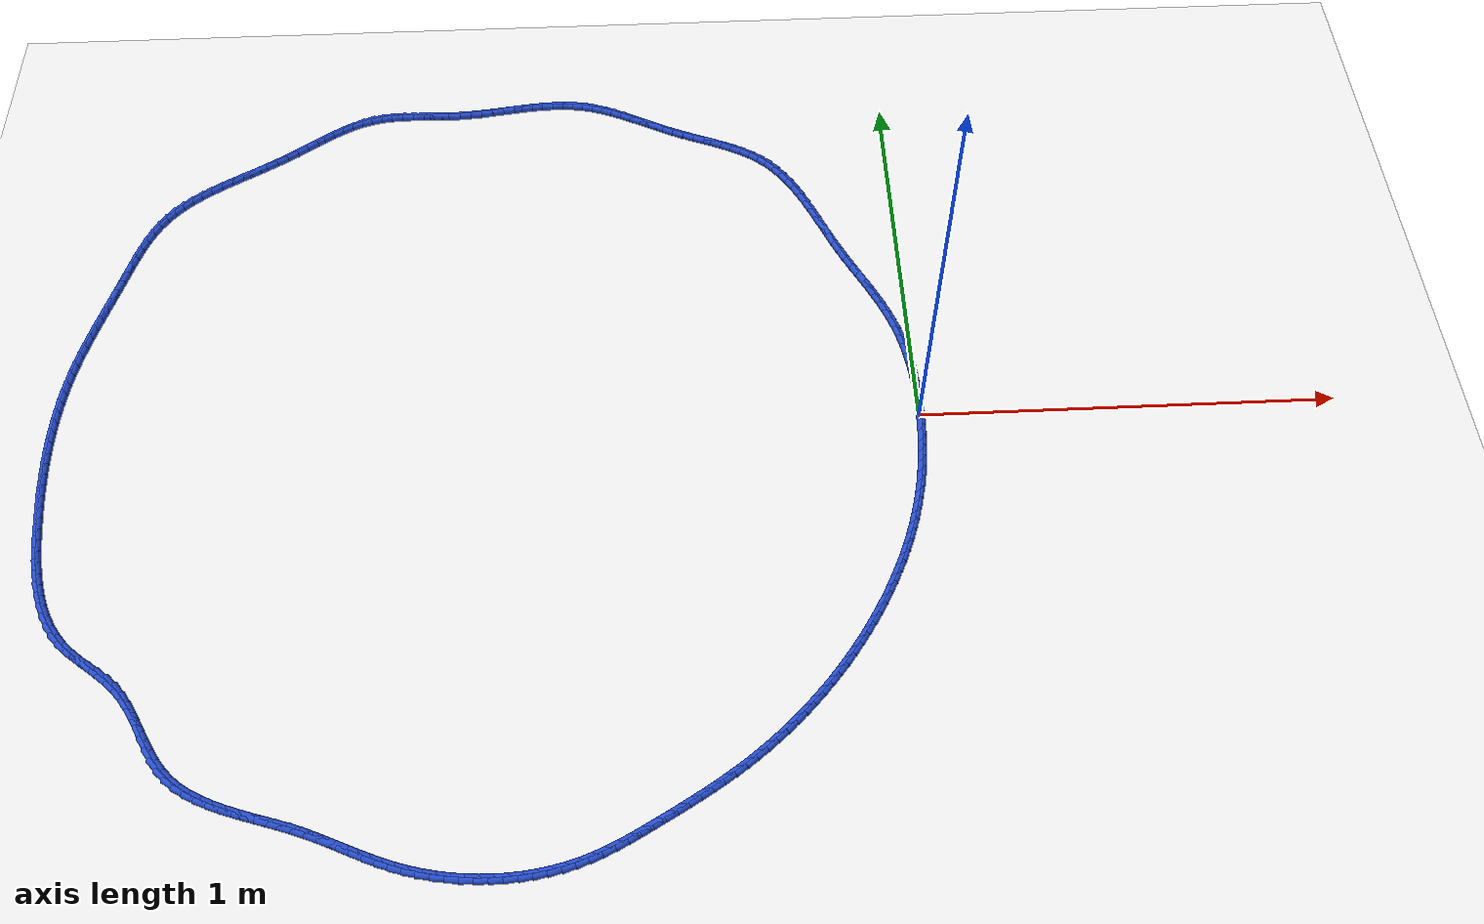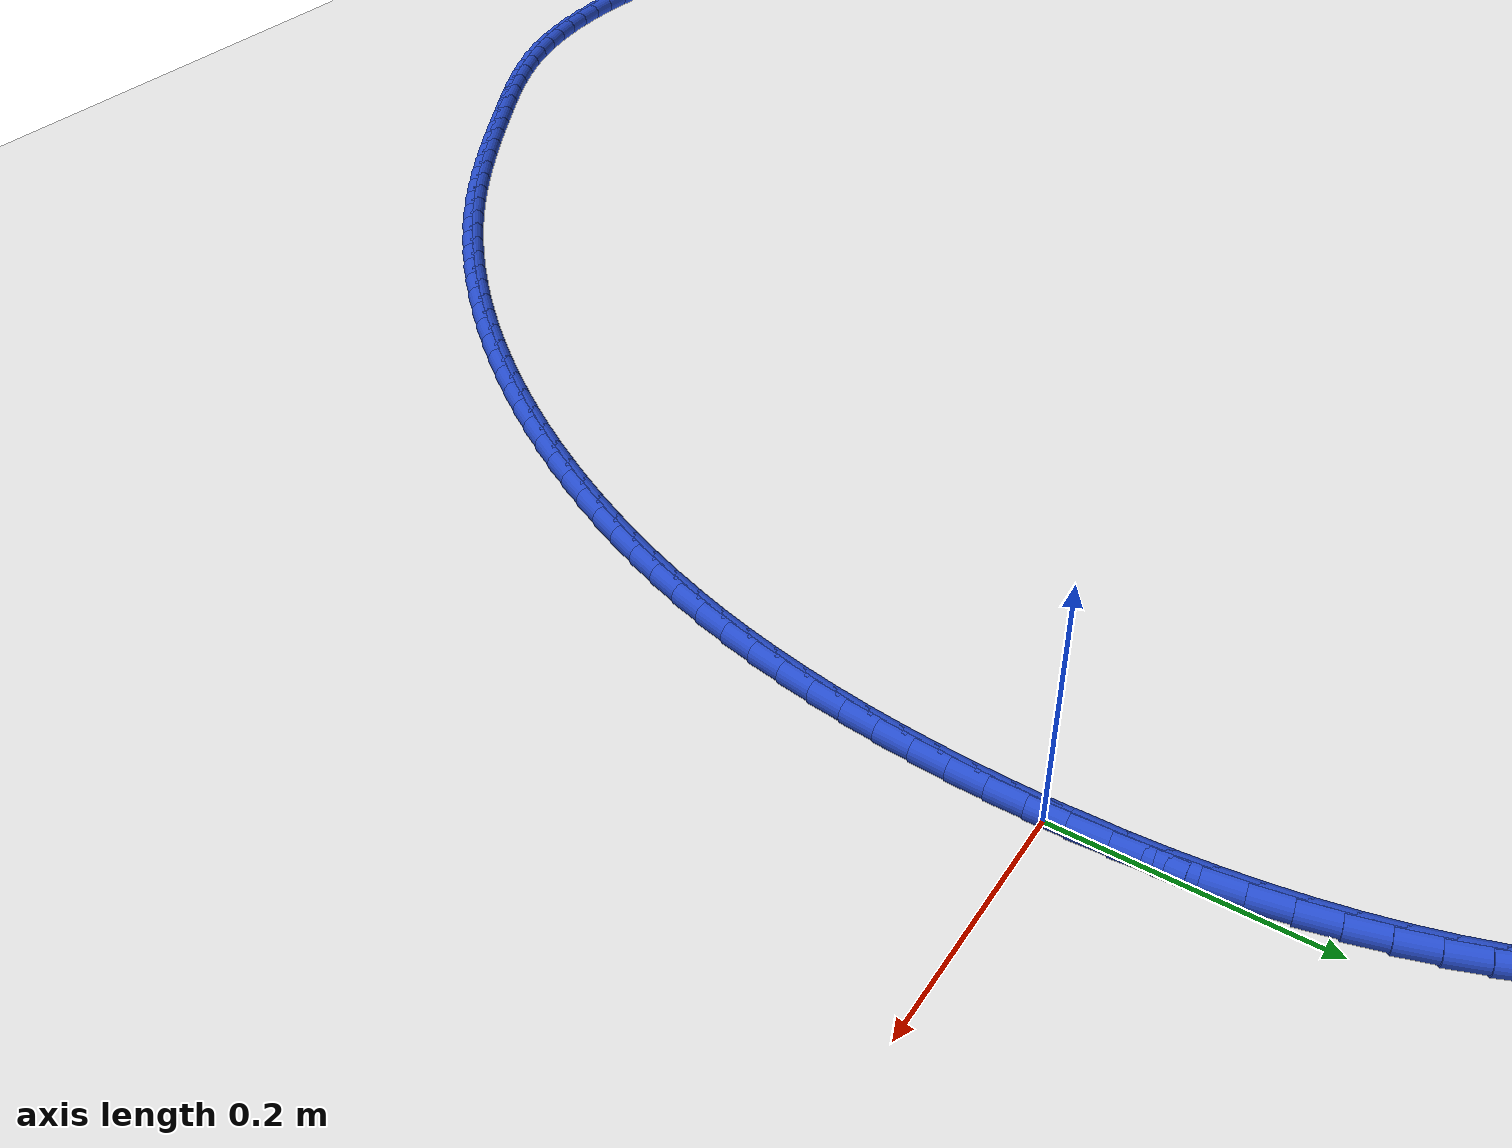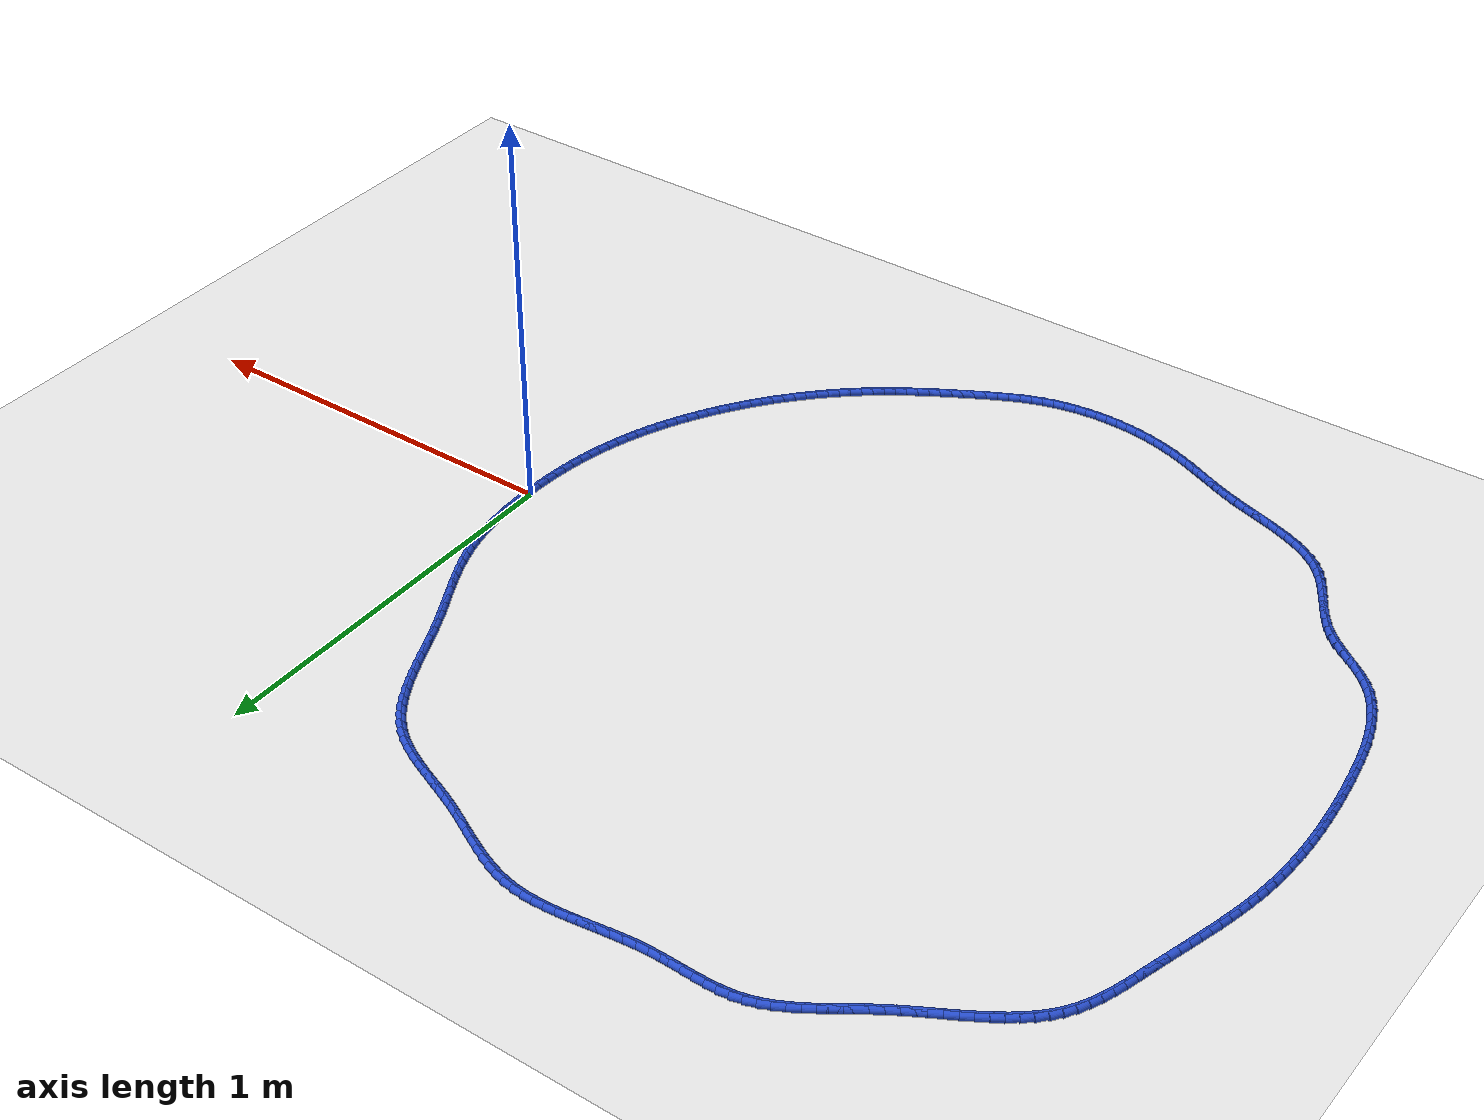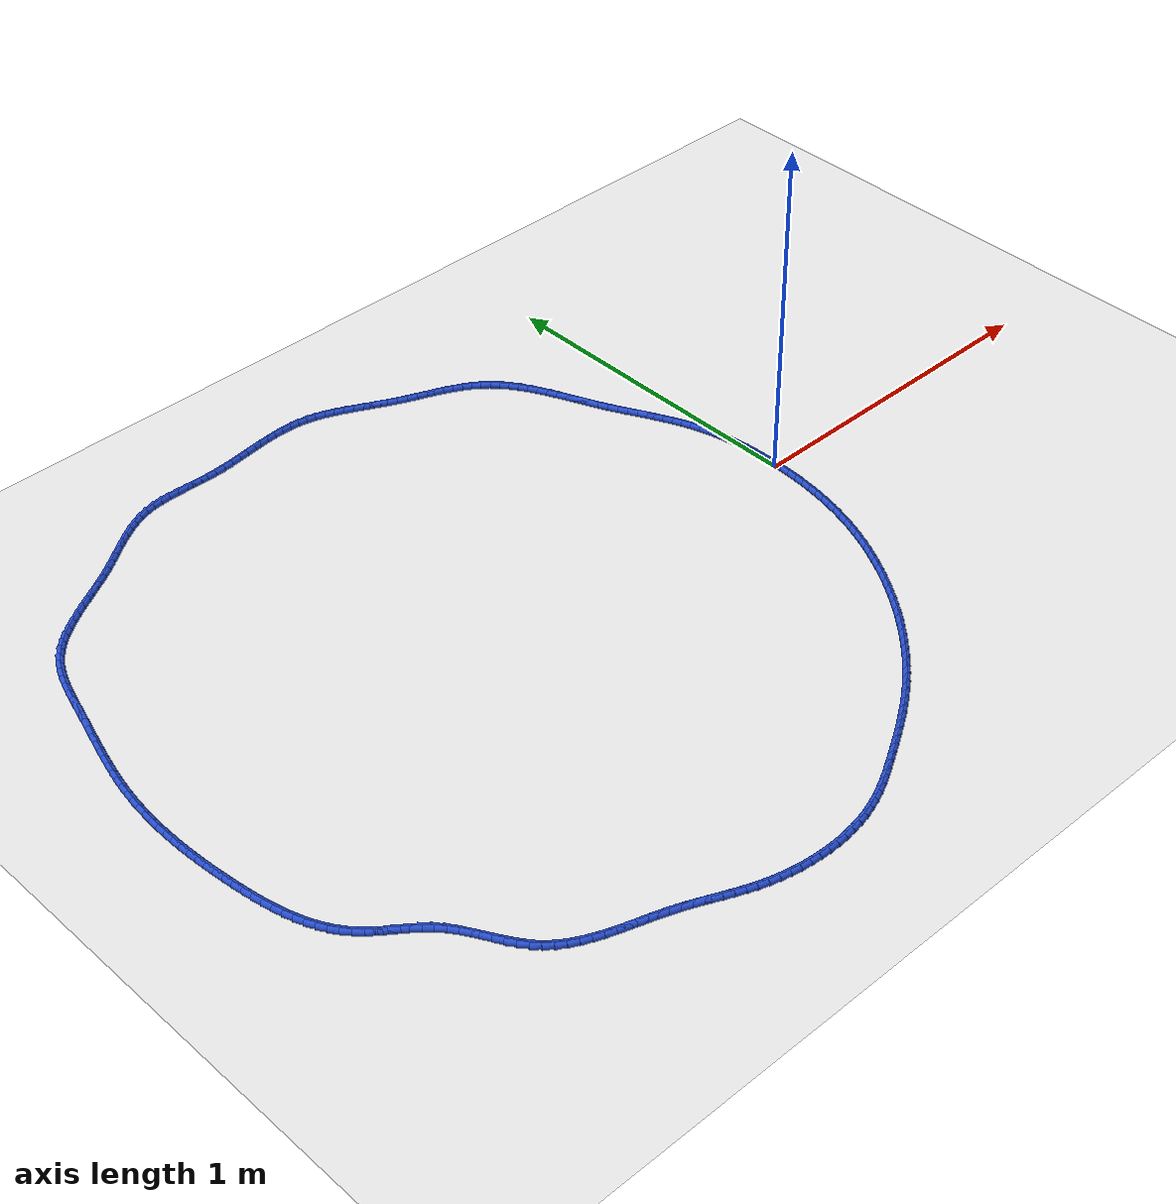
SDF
<sdf version="1.6">
 <world name="default">
  <light name="sun" type="directional">
   <pose>0 0 10 0 -0 0</pose>
   <diffuse>0.8 0.8 0.8 1</diffuse>
   <specular>0.2 0.2 0.2 1</specular>
   <attenuation>
    <range>1000</range>
    <constant>0.9</constant>
    <linear>0.01</linear>
    <quadratic>0.001</quadratic>
   </attenuation>
   <direction>-0.5 0.1 -0.9</direction>
  </light>
  <model name="ground_plane">
   <static>1</static>
   <link name="link">
    <collision name="collision">
     <geometry><plane><normal>0 0 1</normal><size>100 100</size></plane></geometry>
     <surface><friction><ode><mu>100</mu><mu2>50</mu2></ode></friction></surface>
    </collision>
    <visual name="visual">
     <cast_shadows>0</cast_shadows>
     <geometry><plane><normal>0 0 1</normal><size>100 100</size></plane></geometry>
     <material>
      <script><uri>file://media/materials/scripts/gazebo.material</uri><name>Gazebo/WhiteGlow</name></script>
     </material>
    </visual>
   </link>
  </model>
  <gravity>0 0 -9.8</gravity>
  <magnetic_field>6e-06 2.3e-05 -4.2e-05</magnetic_field>
  <atmosphere type="adiabatic"/>
  <physics name="default_physics" default="0" type="ode">
   <max_step_size>0.001</max_step_size>
   <real_time_factor>1</real_time_factor>
   <real_time_update_rate>1000</real_time_update_rate>
  </physics>
  <scene><ambient>0.4 0.4 0.4 1</ambient><background>0.7 0.7 0.7 1</background><shadows>1</shadows></scene>
  <spherical_coordinates>
   <surface_model>EARTH_WGS84</surface_model>
   <latitude_deg>0</latitude_deg>
   <longitude_deg>0</longitude_deg>
   <elevation>0</elevation>
   <heading_deg>0</heading_deg>
  </spherical_coordinates>
  <model name="line">
   <link name="link_0">
    <pose>1.951563910473908e-17 -2.7755575615628914e-17 0.01 0 1.57 -1.5694608289692926</pose>
    <collision name="collision">
     <geometry><cylinder><radius>0.01</radius><length>0.08</length></cylinder></geometry>
    </collision>
    <visual name="visual">
     <material>
      <script><name>Gazebo/Blue</name><uri>file://media/materials/scripts/gazebo.material</uri></script>
     </material>
     <geometry><cylinder><radius>0.01</radius><length>0.08</length></cylinder></geometry>
    </visual>
   </link>
   <link name="link_1">
    <pose>-3.878354684757604e-05 0.029040499390203787 0.01 0 1.57 -1.5432904618189394</pose>
    <collision name="collision">
     <geometry><cylinder><radius>0.01</radius><length>0.08</length></cylinder></geometry>
    </collision>
    <visual name="visual">
     <material>
      <script><name>Gazebo/Blue</name><uri>file://media/materials/scripts/gazebo.material</uri></script>
     </material>
     <geometry><cylinder><radius>0.01</radius><length>0.08</length></cylinder></geometry>
    </visual>
   </link>
   <link name="link_2">
    <pose>-0.0008381468989530367 0.05809473020594538 0.01 0 1.57 -1.5150178035110116</pose>
    <collision name="collision">
     <geometry><cylinder><radius>0.01</radius><length>0.08</length></cylinder></geometry>
    </collision>
    <visual name="visual">
     <material>
      <script><name>Gazebo/Blue</name><uri>file://media/materials/scripts/gazebo.material</uri></script>
     </material>
     <geometry><cylinder><radius>0.01</radius><length>0.08</length></cylinder></geometry>
    </visual>
   </link>
   <link name="link_3">
    <pose>-0.002457510803524472 0.08709664795131193 0.01 0 1.57 -1.4844988249112694</pose>
    <collision name="collision">
     <geometry><cylinder><radius>0.01</radius><length>0.08</length></cylinder></geometry>
    </collision>
    <visual name="visual">
     <material>
      <script><name>Gazebo/Blue</name><uri>file://media/materials/scripts/gazebo.material</uri></script>
     </material>
     <geometry><cylinder><radius>0.01</radius><length>0.08</length></cylinder></geometry>
    </visual>
   </link>
   <link name="link_4">
    <pose>-0.004956296007769978 0.11598020813039038 0.01 0 1.57 -1.451582837474999</pose>
    <collision name="collision">
     <geometry><cylinder><radius>0.01</radius><length>0.08</length></cylinder></geometry>
    </collision>
    <visual name="visual">
     <material>
      <script><name>Gazebo/Blue</name><uri>file://media/materials/scripts/gazebo.material</uri></script>
     </material>
     <geometry><cylinder><radius>0.01</radius><length>0.08</length></cylinder></geometry>
    </visual>
   </link>
   <link name="link_5">
    <pose>-0.008393923258897665 0.1446793662472679 0.01 0 1.57 -1.4161160076519557</pose>
    <collision name="collision">
     <geometry><cylinder><radius>0.01</radius><length>0.08</length></cylinder></geometry>
    </collision>
    <visual name="visual">
     <material>
      <script><name>Gazebo/Blue</name><uri>file://media/materials/scripts/gazebo.material</uri></script>
     </material>
     <geometry><cylinder><radius>0.01</radius><length>0.08</length></cylinder></geometry>
    </visual>
   </link>
   <link name="link_6">
    <pose>-0.012829813304115645 0.17312807780603157 0.01 0 1.57 -1.3779462800567475</pose>
    <collision name="collision">
     <geometry><cylinder><radius>0.01</radius><length>0.08</length></cylinder></geometry>
    </collision>
    <visual name="visual">
     <material>
      <script><name>Gazebo/Blue</name><uri>file://media/materials/scripts/gazebo.material</uri></script>
     </material>
     <geometry><cylinder><radius>0.01</radius><length>0.08</length></cylinder></geometry>
    </visual>
   </link>
   <link name="link_7">
    <pose>-0.018323386890632003 0.2012602983107683 0.01 0 1.57 -1.3369300361527983</pose>
    <collision name="collision">
     <geometry><cylinder><radius>0.01</radius><length>0.08</length></cylinder></geometry>
    </collision>
    <visual name="visual">
     <material>
      <script><name>Gazebo/Blue</name><uri>file://media/materials/scripts/gazebo.material</uri></script>
     </material>
     <geometry><cylinder><radius>0.01</radius><length>0.08</length></cylinder></geometry>
    </visual>
   </link>
   <link name="link_8">
    <pose>-0.024934064765654858 0.22900998326556532 0.01 0 1.57 -1.2929407769741108</pose>
    <collision name="collision">
     <geometry><cylinder><radius>0.01</radius><length>0.08</length></cylinder></geometry>
    </collision>
    <visual name="visual">
     <material>
      <script><name>Gazebo/Blue</name><uri>file://media/materials/scripts/gazebo.material</uri></script>
     </material>
     <geometry><cylinder><radius>0.01</radius><length>0.08</length></cylinder></geometry>
    </visual>
   </link>
   <link name="link_9">
    <pose>-0.032721267676392315 0.25631108817450965 0.01 0 1.57 -1.2460916123326653</pose>
    <collision name="collision">
     <geometry><cylinder><radius>0.01</radius><length>0.08</length></cylinder></geometry>
    </collision>
    <visual name="visual">
     <material>
      <script><name>Gazebo/Blue</name><uri>file://media/materials/scripts/gazebo.material</uri></script>
     </material>
     <geometry><cylinder><radius>0.01</radius><length>0.08</length></cylinder></geometry>
    </visual>
   </link>
   <link name="link_10">
    <pose>-0.04173935688558246 0.28310128655229644 0.01 0 1.57 -1.2013061760137882</pose>
    <collision name="collision">
     <geometry><cylinder><radius>0.01</radius><length>0.08</length></cylinder></geometry>
    </collision>
    <visual name="visual">
     <material>
      <script><name>Gazebo/Blue</name><uri>file://media/materials/scripts/gazebo.material</uri></script>
     </material>
     <geometry><cylinder><radius>0.01</radius><length>0.08</length></cylinder></geometry>
    </visual>
   </link>
   <link name="link_11">
    <pose>-0.051925834778736635 0.30940412677849166 0.01 0 1.57 -1.163805305721505</pose>
    <collision name="collision">
     <geometry><cylinder><radius>0.01</radius><length>0.08</length></cylinder></geometry>
    </collision>
    <visual name="visual">
     <material>
      <script><name>Gazebo/Blue</name><uri>file://media/materials/scripts/gazebo.material</uri></script>
     </material>
     <geometry><cylinder><radius>0.01</radius><length>0.08</length></cylinder></geometry>
    </visual>
   </link>
   <link name="link_12">
    <pose>-0.06310107158197736 0.33532923292154576 0.01 0 1.57 -1.1340337116815435</pose>
    <collision name="collision">
     <geometry><cylinder><radius>0.01</radius><length>0.08</length></cylinder></geometry>
    </collision>
    <visual name="visual">
     <material>
      <script><name>Gazebo/Blue</name><uri>file://media/materials/scripts/gazebo.material</uri></script>
     </material>
     <geometry><cylinder><radius>0.01</radius><length>0.08</length></cylinder></geometry>
    </visual>
   </link>
   <link name="link_13">
    <pose>-0.07508032338043122 0.36098998722538833 0.01 0 1.57 -1.112064558878283</pose>
    <collision name="collision">
     <geometry><cylinder><radius>0.01</radius><length>0.08</length></cylinder></geometry>
    </collision>
    <visual name="visual">
     <material>
      <script><name>Gazebo/Blue</name><uri>file://media/materials/scripts/gazebo.material</uri></script>
     </material>
     <geometry><cylinder><radius>0.01</radius><length>0.08</length></cylinder></geometry>
    </visual>
   </link>
   <link name="link_14">
    <pose>-0.08767884625922485 0.3864997719339496 0.01 0 1.57 -1.0978659826872</pose>
    <collision name="collision">
     <geometry><cylinder><radius>0.01</radius><length>0.08</length></cylinder></geometry>
    </collision>
    <visual name="visual">
     <material>
      <script><name>Gazebo/Blue</name><uri>file://media/materials/scripts/gazebo.material</uri></script>
     </material>
     <geometry><cylinder><radius>0.01</radius><length>0.08</length></cylinder></geometry>
    </visual>
   </link>
   <link name="link_15">
    <pose>-0.10071189630348486 0.41197196929115903 0.01 0 1.57 -1.0913424383070138</pose>
    <collision name="collision">
     <geometry><cylinder><radius>0.01</radius><length>0.08</length></cylinder></geometry>
    </collision>
    <visual name="visual">
     <material>
      <script><name>Gazebo/Blue</name><uri>file://media/materials/scripts/gazebo.material</uri></script>
     </material>
     <geometry><cylinder><radius>0.01</radius><length>0.08</length></cylinder></geometry>
    </visual>
   </link>
   <link name="link_16">
    <pose>-0.11399472959833783 0.4375199615409466 0.01 0 1.57 -1.0923620267805894</pose>
    <collision name="collision">
     <geometry><cylinder><radius>0.01</radius><length>0.08</length></cylinder></geometry>
    </collision>
    <visual name="visual">
     <material>
      <script><name>Gazebo/Blue</name><uri>file://media/materials/scripts/gazebo.material</uri></script>
     </material>
     <geometry><cylinder><radius>0.01</radius><length>0.08</length></cylinder></geometry>
    </visual>
   </link>
   <link name="link_17">
    <pose>-0.12734260222891042 0.4632571309272422 0.01 0 1.57 -1.1007696513155893</pose>
    <collision name="collision">
     <geometry><cylinder><radius>0.01</radius><length>0.08</length></cylinder></geometry>
    </collision>
    <visual name="visual">
     <material>
      <script><name>Gazebo/Blue</name><uri>file://media/materials/scripts/gazebo.material</uri></script>
     </material>
     <geometry><cylinder><radius>0.01</radius><length>0.08</length></cylinder></geometry>
    </visual>
   </link>
   <link name="link_18">
    <pose>-0.1405707702803292 0.4892968596939755 0.01 0 1.57 -1.1163871686910736</pose>
    <collision name="collision">
     <geometry><cylinder><radius>0.01</radius><length>0.08</length></cylinder></geometry>
    </collision>
    <visual name="visual">
     <material>
      <script><name>Gazebo/Blue</name><uri>file://media/materials/scripts/gazebo.material</uri></script>
     </material>
     <geometry><cylinder><radius>0.01</radius><length>0.08</length></cylinder></geometry>
    </visual>
   </link>
   <link name="link_19">
    <pose>-0.1534944898377207 0.5157525300850763 0.01 0 1.57 -1.1375382432080192</pose>
    <collision name="collision">
     <geometry><cylinder><radius>0.01</radius><length>0.08</length></cylinder></geometry>
    </collision>
    <visual name="visual">
     <material>
      <script><name>Gazebo/Blue</name><uri>file://media/materials/scripts/gazebo.material</uri></script>
     </material>
     <geometry><cylinder><radius>0.01</radius><length>0.08</length></cylinder></geometry>
    </visual>
   </link>
   <link name="link_20">
    <pose>-0.1659633427749695 0.5427081145449563 0.01 0 1.57 -1.1540156139257376</pose>
    <collision name="collision">
     <geometry><cylinder><radius>0.01</radius><length>0.08</length></cylinder></geometry>
    </collision>
    <visual name="visual">
     <material>
      <script><name>Gazebo/Blue</name><uri>file://media/materials/scripts/gazebo.material</uri></script>
     </material>
     <geometry><cylinder><radius>0.01</radius><length>0.08</length></cylinder></geometry>
    </visual>
   </link>
   <link name="link_21">
    <pose>-0.1780651583101275 0.5700434589158023 0.01 0 1.57 -1.161786566662351</pose>
    <collision name="collision">
     <geometry><cylinder><radius>0.01</radius><length>0.08</length></cylinder></geometry>
    </collision>
    <visual name="visual">
     <material>
      <script><name>Gazebo/Blue</name><uri>file://media/materials/scripts/gazebo.material</uri></script>
     </material>
     <geometry><cylinder><radius>0.01</radius><length>0.08</length></cylinder></geometry>
    </visual>
   </link>
   <link name="link_22">
    <pose>-0.18998879220959417 0.5975518510715672 0.01 0 1.57 -1.1609973132092868</pose>
    <collision name="collision">
     <geometry><cylinder><radius>0.01</radius><length>0.08</length></cylinder></geometry>
    </collision>
    <visual name="visual">
     <material>
      <script><name>Gazebo/Blue</name><uri>file://media/materials/scripts/gazebo.material</uri></script>
     </material>
     <geometry><cylinder><radius>0.01</radius><length>0.08</length></cylinder></geometry>
    </visual>
   </link>
   <link name="link_23">
    <pose>-0.20192346564646488 0.6250262658114543 0.01 0 1.57 -1.1516158661648064</pose>
    <collision name="collision">
     <geometry><cylinder><radius>0.01</radius><length>0.08</length></cylinder></geometry>
    </collision>
    <visual name="visual">
     <material>
      <script><name>Gazebo/Blue</name><uri>file://media/materials/scripts/gazebo.material</uri></script>
     </material>
     <geometry><cylinder><radius>0.01</radius><length>0.08</length></cylinder></geometry>
    </visual>
   </link>
   <link name="link_24">
    <pose>-0.21405839979383506 0.6522596779346681 0.01 0 1.57 -1.133416180992991</pose>
    <collision name="collision">
     <geometry><cylinder><radius>0.01</radius><length>0.08</length></cylinder></geometry>
    </collision>
    <visual name="visual">
     <material>
      <script><name>Gazebo/Blue</name><uri>file://media/materials/scripts/gazebo.material</uri></script>
     </material>
     <geometry><cylinder><radius>0.01</radius><length>0.08</length></cylinder></geometry>
    </visual>
   </link>
   <link name="link_25">
    <pose>-0.2265828158248002 0.6790450622404122 0.01 0 1.57 -1.1059874194147943</pose>
    <collision name="collision">
     <geometry><cylinder><radius>0.01</radius><length>0.08</length></cylinder></geometry>
    </collision>
    <visual name="visual">
     <material>
      <script><name>Gazebo/Blue</name><uri>file://media/materials/scripts/gazebo.material</uri></script>
     </material>
     <geometry><cylinder><radius>0.01</radius><length>0.08</length></cylinder></geometry>
    </visual>
   </link>
   <link name="link_26">
    <pose>-0.23968593491245577 0.7051753935278908 0.01 0 1.57 -1.0687585267305069</pose>
    <collision name="collision">
     <geometry><cylinder><radius>0.01</radius><length>0.08</length></cylinder></geometry>
    </collision>
    <visual name="visual">
     <material>
      <script><name>Gazebo/Blue</name><uri>file://media/materials/scripts/gazebo.material</uri></script>
     </material>
     <geometry><cylinder><radius>0.01</radius><length>0.08</length></cylinder></geometry>
    </visual>
   </link>
   <link name="link_27">
    <pose>-0.2535569782298973 0.7304436465963081 0.01 0 1.57 -1.0210497358509645</pose>
    <collision name="collision">
     <geometry><cylinder><radius>0.01</radius><length>0.08</length></cylinder></geometry>
    </collision>
    <visual name="visual">
     <material>
      <script><name>Gazebo/Blue</name><uri>file://media/materials/scripts/gazebo.material</uri></script>
     </material>
     <geometry><cylinder><radius>0.01</radius><length>0.08</length></cylinder></geometry>
    </visual>
   </link>
   <link name="link_28">
    <pose>-0.26838516695022013 0.7546427962448679 0.01 0 1.57 -0.9621685555784789</pose>
    <collision name="collision">
     <geometry><cylinder><radius>0.01</radius><length>0.08</length></cylinder></geometry>
    </collision>
    <visual name="visual">
     <material>
      <script><name>Gazebo/Blue</name><uri>file://media/materials/scripts/gazebo.material</uri></script>
     </material>
     <geometry><cylinder><radius>0.01</radius><length>0.08</length></cylinder></geometry>
    </visual>
   </link>
   <link name="link_29">
    <pose>-0.28435972224651956 0.7775658172727737 0.01 0 1.57 -0.891570905380093</pose>
    <collision name="collision">
     <geometry><cylinder><radius>0.01</radius><length>0.08</length></cylinder></geometry>
    </collision>
    <visual name="visual">
     <material>
      <script><name>Gazebo/Blue</name><uri>file://media/materials/scripts/gazebo.material</uri></script>
     </material>
     <geometry><cylinder><radius>0.01</radius><length>0.08</length></cylinder></geometry>
    </visual>
   </link>
   <link name="link_30">
    <pose>-0.30166986529189144 0.7990056844792305 0.01 0 1.57 -0.8091009865879865</pose>
    <collision name="collision">
     <geometry><cylinder><radius>0.01</radius><length>0.08</length></cylinder></geometry>
    </collision>
    <visual name="visual">
     <material>
      <script><name>Gazebo/Blue</name><uri>file://media/materials/scripts/gazebo.material</uri></script>
     </material>
     <geometry><cylinder><radius>0.01</radius><length>0.08</length></cylinder></geometry>
    </visual>
   </link>
   <link name="link_31">
    <pose>-0.3205048172594309 0.8187553726634414 0.01 0 1.57 -0.7154814919595996</pose>
    <collision name="collision">
     <geometry><cylinder><radius>0.01</radius><length>0.08</length></cylinder></geometry>
    </collision>
    <visual name="visual">
     <material>
      <script><name>Gazebo/Blue</name><uri>file://media/materials/scripts/gazebo.material</uri></script>
     </material>
     <geometry><cylinder><radius>0.01</radius><length>0.08</length></cylinder></geometry>
    </visual>
   </link>
   <link name="link_32">
    <pose>-0.34105053470995733 0.8366117592712243 0.01 0 1.57 -0.6218386338732178</pose>
    <collision name="collision">
     <geometry><cylinder><radius>0.01</radius><length>0.08</length></cylinder></geometry>
    </collision>
    <visual name="visual">
     <material>
      <script><name>Gazebo/Blue</name><uri>file://media/materials/scripts/gazebo.material</uri></script>
     </material>
     <geometry><cylinder><radius>0.01</radius><length>0.08</length></cylinder></geometry>
    </visual>
   </link>
   <link name="link_33">
    <pose>-0.36332338662063507 0.8525744534522284 0.01 0 1.57 -0.5436751232413074</pose>
    <collision name="collision">
     <geometry><cylinder><radius>0.01</radius><length>0.08</length></cylinder></geometry>
    </collision>
    <visual name="visual">
     <material>
      <script><name>Gazebo/Blue</name><uri>file://media/materials/scripts/gazebo.material</uri></script>
     </material>
     <geometry><cylinder><radius>0.01</radius><length>0.08</length></cylinder></geometry>
    </visual>
   </link>
   <link name="link_34">
    <pose>-0.3870909766184695 0.866940448293091 0.01 0 1.57 -0.48218282550513586</pose>
    <collision name="collision">
     <geometry><cylinder><radius>0.01</radius><length>0.08</length></cylinder></geometry>
    </collision>
    <visual name="visual">
     <material>
      <script><name>Gazebo/Blue</name><uri>file://media/materials/scripts/gazebo.material</uri></script>
     </material>
     <geometry><cylinder><radius>0.01</radius><length>0.08</length></cylinder></geometry>
    </visual>
   </link>
   <link name="link_35">
    <pose>-0.41210107581772487 0.8800304454504557 0.01 0 1.57 -0.4366647646260139</pose>
    <collision name="collision">
     <geometry><cylinder><radius>0.01</radius><length>0.08</length></cylinder></geometry>
    </collision>
    <visual name="visual">
     <material>
      <script><name>Gazebo/Blue</name><uri>file://media/materials/scripts/gazebo.material</uri></script>
     </material>
     <geometry><cylinder><radius>0.01</radius><length>0.08</length></cylinder></geometry>
    </visual>
   </link>
   <link name="link_36">
    <pose>-0.4381014553326658 0.8921651465809661 0.01 0 1.57 -0.4061795346657899</pose>
    <collision name="collision">
     <geometry><cylinder><radius>0.01</radius><length>0.08</length></cylinder></geometry>
    </collision>
    <visual name="visual">
     <material>
      <script><name>Gazebo/Blue</name><uri>file://media/materials/scripts/gazebo.material</uri></script>
     </material>
     <geometry><cylinder><radius>0.01</radius><length>0.08</length></cylinder></geometry>
    </visual>
   </link>
   <link name="link_37">
    <pose>-0.4648398862775566 0.9036652533412662 0.01 0 1.57 -0.3898601877596033</pose>
    <collision name="collision">
     <geometry><cylinder><radius>0.01</radius><length>0.08</length></cylinder></geometry>
    </collision>
    <visual name="visual">
     <material>
      <script><name>Gazebo/Blue</name><uri>file://media/materials/scripts/gazebo.material</uri></script>
     </material>
     <geometry><cylinder><radius>0.01</radius><length>0.08</length></cylinder></geometry>
    </visual>
   </link>
   <link name="link_38">
    <pose>-0.49206413976666136 0.9148514673879994 0.01 0 1.57 -0.3870784998192405</pose>
    <collision name="collision">
     <geometry><cylinder><radius>0.01</radius><length>0.08</length></cylinder></geometry>
    </collision>
    <visual name="visual">
     <material>
      <script><name>Gazebo/Blue</name><uri>file://media/materials/scripts/gazebo.material</uri></script>
     </material>
     <geometry><cylinder><radius>0.01</radius><length>0.08</length></cylinder></geometry>
    </visual>
   </link>
   <link name="link_39">
    <pose>-0.5195219869142449 0.9260444903778096 0.01 0 1.57 -0.397506068324324</pose>
    <collision name="collision">
     <geometry><cylinder><radius>0.01</radius><length>0.08</length></cylinder></geometry>
    </collision>
    <visual name="visual">
     <material>
      <script><name>Gazebo/Blue</name><uri>file://media/materials/scripts/gazebo.material</uri></script>
     </material>
     <geometry><cylinder><radius>0.01</radius><length>0.08</length></cylinder></geometry>
    </visual>
   </link>
   <link name="link_40">
    <pose>-0.5469611988345714 0.9375650239673404 0.01 0 1.57 -0.4209592803566281</pose>
    <collision name="collision">
     <geometry><cylinder><radius>0.01</radius><length>0.08</length></cylinder></geometry>
    </collision>
    <visual name="visual">
     <material>
      <script><name>Gazebo/Blue</name><uri>file://media/materials/scripts/gazebo.material</uri></script>
     </material>
     <geometry><cylinder><radius>0.01</radius><length>0.08</length></cylinder></geometry>
    </visual>
   </link>
   <link name="link_41">
    <pose>-0.574131566904398 0.9497298396941195 0.01 0 1.57 -0.44840053376011474</pose>
    <collision name="collision">
     <geometry><cylinder><radius>0.01</radius><length>0.08</length></cylinder></geometry>
    </collision>
    <visual name="visual">
     <material>
      <script><name>Gazebo/Blue</name><uri>file://media/materials/scripts/gazebo.material</uri></script>
     </material>
     <geometry><cylinder><radius>0.01</radius><length>0.08</length></cylinder></geometry>
    </visual>
   </link>
   <link name="link_42">
    <pose>-0.6009083137038936 0.9626117014125278 0.01 0 1.57 -0.46549211728601964</pose>
    <collision name="collision">
     <geometry><cylinder><radius>0.01</radius><length>0.08</length></cylinder></geometry>
    </collision>
    <visual name="visual">
     <material>
      <script><name>Gazebo/Blue</name><uri>file://media/materials/scripts/gazebo.material</uri></script>
     </material>
     <geometry><cylinder><radius>0.01</radius><length>0.08</length></cylinder></geometry>
    </visual>
   </link>
   <link name="link_43">
    <pose>-0.6273635436000568 0.9759003688491711 0.01 0 1.57 -0.4709485560047609</pose>
    <collision name="collision">
     <geometry><cylinder><radius>0.01</radius><length>0.08</length></cylinder></geometry>
    </collision>
    <visual name="visual">
     <material>
      <script><name>Gazebo/Blue</name><uri>file://media/materials/scripts/gazebo.material</uri></script>
     </material>
     <geometry><cylinder><radius>0.01</radius><length>0.08</length></cylinder></geometry>
    </visual>
   </link>
   <link name="link_44">
    <pose>-0.6535865882536065 0.9892520886022375 0.01 0 1.57 -0.46459571442858605</pose>
    <collision name="collision">
     <geometry><cylinder><radius>0.01</radius><length>0.08</length></cylinder></geometry>
    </collision>
    <visual name="visual">
     <material>
      <script><name>Gazebo/Blue</name><uri>file://media/materials/scripts/gazebo.material</uri></script>
     </material>
     <geometry><cylinder><radius>0.01</radius><length>0.08</length></cylinder></geometry>
    </visual>
   </link>
   <link name="link_45">
    <pose>-0.6796667793252615 1.002323107269916 0.01 0 1.57 -0.446075115598375</pose>
    <collision name="collision">
     <geometry><cylinder><radius>0.01</radius><length>0.08</length></cylinder></geometry>
    </collision>
    <visual name="visual">
     <material>
      <script><name>Gazebo/Blue</name><uri>file://media/materials/scripts/gazebo.material</uri></script>
     </material>
     <geometry><cylinder><radius>0.01</radius><length>0.08</length></cylinder></geometry>
    </visual>
   </link>
   <link name="link_46">
    <pose>-0.7056934484757403 1.0147696714503944 0.01 0 1.57 -0.4148561046462073</pose>
    <collision name="collision">
     <geometry><cylinder><radius>0.01</radius><length>0.08</length></cylinder></geometry>
    </collision>
    <visual name="visual">
     <material>
      <script><name>Gazebo/Blue</name><uri>file://media/materials/scripts/gazebo.material</uri></script>
     </material>
     <geometry><cylinder><radius>0.01</radius><length>0.08</length></cylinder></geometry>
    </visual>
   </link>
   <link name="link_47">
    <pose>-0.7317559273657617 1.026248027741861 0.01 0 1.57 -0.37030473141281095</pose>
    <collision name="collision">
     <geometry><cylinder><radius>0.01</radius><length>0.08</length></cylinder></geometry>
    </collision>
    <visual name="visual">
     <material>
      <script><name>Gazebo/Blue</name><uri>file://media/materials/scripts/gazebo.material</uri></script>
     </material>
     <geometry><cylinder><radius>0.01</radius><length>0.08</length></cylinder></geometry>
    </visual>
   </link>
   <link name="link_48">
    <pose>-0.7579435476560444 1.0364144227425043 0.01 0 1.57 -0.3118320176358554</pose>
    <collision name="collision">
     <geometry><cylinder><radius>0.01</radius><length>0.08</length></cylinder></geometry>
    </collision>
    <visual name="visual">
     <material>
      <script><name>Gazebo/Blue</name><uri>file://media/materials/scripts/gazebo.material</uri></script>
     </material>
     <geometry><cylinder><radius>0.01</radius><length>0.08</length></cylinder></geometry>
    </visual>
   </link>
   <link name="link_49">
    <pose>-0.7843456410073073 1.044925103050513 0.01 0 1.57 -0.23914601775955457</pose>
    <collision name="collision">
     <geometry><cylinder><radius>0.01</radius><length>0.08</length></cylinder></geometry>
    </collision>
    <visual name="visual">
     <material>
      <script><name>Gazebo/Blue</name><uri>file://media/materials/scripts/gazebo.material</uri></script>
     </material>
     <geometry><cylinder><radius>0.01</radius><length>0.08</length></cylinder></geometry>
    </visual>
   </link>
   <link name="link_50">
    <pose>-0.8110515390802692 1.0514363152640749 0.01 0 1.57 -0.15546103807533657</pose>
    <collision name="collision">
     <geometry><cylinder><radius>0.01</radius><length>0.08</length></cylinder></geometry>
    </collision>
    <visual name="visual">
     <material>
      <script><name>Gazebo/Blue</name><uri>file://media/materials/scripts/gazebo.material</uri></script>
     </material>
     <geometry><cylinder><radius>0.01</radius><length>0.08</length></cylinder></geometry>
    </visual>
   </link>
   <link name="link_51">
    <pose>-0.8381366836914228 1.0556812525932815 0.01 0 1.57 -0.0779235943004407</pose>
    <collision name="collision">
     <geometry><cylinder><radius>0.01</radius><length>0.08</length></cylinder></geometry>
    </collision>
    <visual name="visual">
     <material>
      <script><name>Gazebo/Blue</name><uri>file://media/materials/scripts/gazebo.material</uri></script>
     </material>
     <geometry><cylinder><radius>0.01</radius><length>0.08</length></cylinder></geometry>
    </visual>
   </link>
   <link name="link_52">
    <pose>-0.8655984617536748 1.0578255148523399 0.01 0 1.57 -0.012949238469325115</pose>
    <collision name="collision">
     <geometry><cylinder><radius>0.01</radius><length>0.08</length></cylinder></geometry>
    </collision>
    <visual name="visual">
     <material>
      <script><name>Gazebo/Blue</name><uri>file://media/materials/scripts/gazebo.material</uri></script>
     </material>
     <geometry><cylinder><radius>0.01</radius><length>0.08</length></cylinder></geometry>
    </visual>
   </link>
   <link name="link_53">
    <pose>-0.893407014901608 1.058185634567389 0.01 0 1.57 0.039350918258431636</pose>
    <collision name="collision">
     <geometry><cylinder><radius>0.01</radius><length>0.08</length></cylinder></geometry>
    </collision>
    <visual name="visual">
     <material>
      <script><name>Gazebo/Blue</name><uri>file://media/materials/scripts/gazebo.material</uri></script>
     </material>
     <geometry><cylinder><radius>0.01</radius><length>0.08</length></cylinder></geometry>
    </visual>
   </link>
   <link name="link_54">
    <pose>-0.9215324564790256 1.0570783009891298 0.01 0 1.57 0.07930895614756005</pose>
    <collision name="collision">
     <geometry><cylinder><radius>0.01</radius><length>0.08</length></cylinder></geometry>
    </collision>
    <visual name="visual">
     <material>
      <script><name>Gazebo/Blue</name><uri>file://media/materials/scripts/gazebo.material</uri></script>
     </material>
     <geometry><cylinder><radius>0.01</radius><length>0.08</length></cylinder></geometry>
    </visual>
   </link>
   <link name="link_55">
    <pose>-0.9499448998297297 1.0548202033682617 0.01 0 1.57 0.10744027245277923</pose>
    <collision name="collision">
     <geometry><cylinder><radius>0.01</radius><length>0.08</length></cylinder></geometry>
    </collision>
    <visual name="visual">
     <material>
      <script><name>Gazebo/Blue</name><uri>file://media/materials/scripts/gazebo.material</uri></script>
     </material>
     <geometry><cylinder><radius>0.01</radius><length>0.08</length></cylinder></geometry>
    </visual>
   </link>
   <link name="link_56">
    <pose>-0.9786144582975231 1.0517280309554844 0.01 0 1.57 0.12426843281583863</pose>
    <collision name="collision">
     <geometry><cylinder><radius>0.01</radius><length>0.08</length></cylinder></geometry>
    </collision>
    <visual name="visual">
     <material>
      <script><name>Gazebo/Blue</name><uri>file://media/materials/scripts/gazebo.material</uri></script>
     </material>
     <geometry><cylinder><radius>0.01</radius><length>0.08</length></cylinder></geometry>
    </visual>
   </link>
   <link name="link_57">
    <pose>-1.0075112452262078 1.0481184730014979 0.01 0 1.57 0.1302218783436842</pose>
    <collision name="collision">
     <geometry><cylinder><radius>0.01</radius><length>0.08</length></cylinder></geometry>
    </collision>
    <visual name="visual">
     <material>
      <script><name>Gazebo/Blue</name><uri>file://media/materials/scripts/gazebo.material</uri></script>
     </material>
     <geometry><cylinder><radius>0.01</radius><length>0.08</length></cylinder></geometry>
    </visual>
   </link>
   <link name="link_58">
    <pose>-1.0366053739595869 1.044308218757002 0.01 0 1.57 0.12558511363762795</pose>
    <collision name="collision">
     <geometry><cylinder><radius>0.01</radius><length>0.08</length></cylinder></geometry>
    </collision>
    <visual name="visual">
     <material>
      <script><name>Gazebo/Blue</name><uri>file://media/materials/scripts/gazebo.material</uri></script>
     </material>
     <geometry><cylinder><radius>0.01</radius><length>0.08</length></cylinder></geometry>
    </visual>
   </link>
   <link name="link_59">
    <pose>-1.065866957841463 1.0406139574726965 0.01 0 1.57 0.11048944051230561</pose>
    <collision name="collision">
     <geometry><cylinder><radius>0.01</radius><length>0.08</length></cylinder></geometry>
    </collision>
    <visual name="visual">
     <material>
      <script><name>Gazebo/Blue</name><uri>file://media/materials/scripts/gazebo.material</uri></script>
     </material>
     <geometry><cylinder><radius>0.01</radius><length>0.08</length></cylinder></geometry>
    </visual>
   </link>
   <link name="link_60">
    <pose>-1.0952661102156378 1.037352378399281 0.01 0 1.57 0.08493502554246739</pose>
    <collision name="collision">
     <geometry><cylinder><radius>0.01</radius><length>0.08</length></cylinder></geometry>
    </collision>
    <visual name="visual">
     <material>
      <script><name>Gazebo/Blue</name><uri>file://media/materials/scripts/gazebo.material</uri></script>
     </material>
     <geometry><cylinder><radius>0.01</radius><length>0.08</length></cylinder></geometry>
    </visual>
   </link>
   <link name="link_61">
    <pose>-1.1247729444259147 1.0348401707874557 0.01 0 1.57 0.04884336234892613</pose>
    <collision name="collision">
     <geometry><cylinder><radius>0.01</radius><length>0.08</length></cylinder></geometry>
    </collision>
    <visual name="visual">
     <material>
      <script><name>Gazebo/Blue</name><uri>file://media/materials/scripts/gazebo.material</uri></script>
     </material>
     <geometry><cylinder><radius>0.01</radius><length>0.08</length></cylinder></geometry>
    </visual>
   </link>
   <link name="link_62">
    <pose>-1.154357572230155 1.0333940078842734 0.01 0 1.57 0.007734150934706092</pose>
    <collision name="collision">
     <geometry><cylinder><radius>0.01</radius><length>0.08</length></cylinder></geometry>
    </collision>
    <visual name="visual">
     <material>
      <script><name>Gazebo/Blue</name><uri>file://media/materials/scripts/gazebo.material</uri></script>
     </material>
     <geometry><cylinder><radius>0.01</radius><length>0.08</length></cylinder></geometry>
    </visual>
   </link>
   <link name="link_63">
    <pose>-1.1839736931406617 1.0331649477677962 0.01 0 1.57 -0.019136045392431862</pose>
    <collision name="collision">
     <geometry><cylinder><radius>0.01</radius><length>0.08</length></cylinder></geometry>
    </collision>
    <visual name="visual">
     <material>
      <script><name>Gazebo/Blue</name><uri>file://media/materials/scripts/gazebo.material</uri></script>
     </material>
     <geometry><cylinder><radius>0.01</radius><length>0.08</length></cylinder></geometry>
    </visual>
   </link>
   <link name="link_64">
    <pose>-1.2135181569718128 1.03373038098878 0.01 0 1.57 -0.02769266900549229</pose>
    <collision name="collision">
     <geometry><cylinder><radius>0.01</radius><length>0.08</length></cylinder></geometry>
    </collision>
    <visual name="visual">
     <material>
      <script><name>Gazebo/Blue</name><uri>file://media/materials/scripts/gazebo.material</uri></script>
     </material>
     <geometry><cylinder><radius>0.01</radius><length>0.08</length></cylinder></geometry>
    </visual>
   </link>
   <link name="link_65">
    <pose>-1.2428755128457583 1.0345435724129768 0.01 0 1.57 -0.017696245295093664</pose>
    <collision name="collision">
     <geometry><cylinder><radius>0.01</radius><length>0.08</length></cylinder></geometry>
    </collision>
    <visual name="visual">
     <material>
      <script><name>Gazebo/Blue</name><uri>file://media/materials/scripts/gazebo.material</uri></script>
     </material>
     <geometry><cylinder><radius>0.01</radius><length>0.08</length></cylinder></geometry>
    </visual>
   </link>
   <link name="link_66">
    <pose>-1.2719303098846457 1.0350577869061361 0.01 0 1.57 0.011575417395932387</pose>
    <collision name="collision">
     <geometry><cylinder><radius>0.01</radius><length>0.08</length></cylinder></geometry>
    </collision>
    <visual name="visual">
     <material>
      <script><name>Gazebo/Blue</name><uri>file://media/materials/scripts/gazebo.material</uri></script>
     </material>
     <geometry><cylinder><radius>0.01</radius><length>0.08</length></cylinder></geometry>
    </visual>
   </link>
   <link name="link_67">
    <pose>-1.3005670972106225 1.0347262893340088 0.01 0 1.57 0.06126631450009764</pose>
    <collision name="collision">
     <geometry><cylinder><radius>0.01</radius><length>0.08</length></cylinder></geometry>
    </collision>
    <visual name="visual">
     <material>
      <script><name>Gazebo/Blue</name><uri>file://media/materials/scripts/gazebo.material</uri></script>
     </material>
     <geometry><cylinder><radius>0.01</radius><length>0.08</length></cylinder></geometry>
    </visual>
   </link>
   <link name="link_68">
    <pose>-1.3286704239458378 1.0330023445623455 0.01 0 1.57 0.1326423750290049</pose>
    <collision name="collision">
     <geometry><cylinder><radius>0.01</radius><length>0.08</length></cylinder></geometry>
    </collision>
    <visual name="visual">
     <material>
      <script><name>Gazebo/Blue</name><uri>file://media/materials/scripts/gazebo.material</uri></script>
     </material>
     <geometry><cylinder><radius>0.01</radius><length>0.08</length></cylinder></geometry>
    </visual>
   </link>
   <link name="link_69">
    <pose>-1.3561248392124394 1.0293392174568976 0.01 0 1.57 0.22629027265547483</pose>
    <collision name="collision">
     <geometry><cylinder><radius>0.01</radius><length>0.08</length></cylinder></geometry>
    </collision>
    <visual name="visual">
     <material>
      <script><name>Gazebo/Blue</name><uri>file://media/materials/scripts/gazebo.material</uri></script>
     </material>
     <geometry><cylinder><radius>0.01</radius><length>0.08</length></cylinder></geometry>
    </visual>
   </link>
   <link name="link_70">
    <pose>-1.3828159899018309 1.023194016830372 0.01 0 1.57 0.3291289269061262</pose>
    <collision name="collision">
     <geometry><cylinder><radius>0.01</radius><length>0.08</length></cylinder></geometry>
    </collision>
    <visual name="visual">
     <material>
      <script><name>Gazebo/Blue</name><uri>file://media/materials/scripts/gazebo.material</uri></script>
     </material>
     <geometry><cylinder><radius>0.01</radius><length>0.08</length></cylinder></geometry>
    </visual>
   </link>
   <link name="link_71">
    <pose>-1.4087215058885403 1.0143459389527039 0.01 0 1.57 0.4177531818009058</pose>
    <collision name="collision">
     <geometry><cylinder><radius>0.01</radius><length>0.08</length></cylinder></geometry>
    </collision>
    <visual name="visual">
     <material>
      <script><name>Gazebo/Blue</name><uri>file://media/materials/scripts/gazebo.material</uri></script>
     </material>
     <geometry><cylinder><radius>0.01</radius><length>0.08</length></cylinder></geometry>
    </visual>
   </link>
   <link name="link_72">
    <pose>-1.4339790652732687 1.0031346046903042 0.01 0 1.57 0.4890679003779238</pose>
    <collision name="collision">
     <geometry><cylinder><radius>0.01</radius><length>0.08</length></cylinder></geometry>
    </collision>
    <visual name="visual">
     <material>
      <script><name>Gazebo/Blue</name><uri>file://media/materials/scripts/gazebo.material</uri></script>
     </material>
     <geometry><cylinder><radius>0.01</radius><length>0.08</length></cylinder></geometry>
    </visual>
   </link>
   <link name="link_73">
    <pose>-1.4587423802896686 0.9899557800022617 0.01 0 1.57 0.5433311350675442</pose>
    <collision name="collision">
     <geometry><cylinder><radius>0.01</radius><length>0.08</length></cylinder></geometry>
    </collision>
    <visual name="visual">
     <material>
      <script><name>Gazebo/Blue</name><uri>file://media/materials/scripts/gazebo.material</uri></script>
     </material>
     <geometry><cylinder><radius>0.01</radius><length>0.08</length></cylinder></geometry>
    </visual>
   </link>
   <link name="link_74">
    <pose>-1.4831651631713947 0.9752052308476643 0.01 0 1.57 0.5813806939581277</pose>
    <collision name="collision">
     <geometry><cylinder><radius>0.01</radius><length>0.08</length></cylinder></geometry>
    </collision>
    <visual name="visual">
     <material>
      <script><name>Gazebo/Blue</name><uri>file://media/materials/scripts/gazebo.material</uri></script>
     </material>
     <geometry><cylinder><radius>0.01</radius><length>0.08</length></cylinder></geometry>
    </visual>
   </link>
   <link name="link_75">
    <pose>-1.5074011261521005 0.959278723185601 0.01 0 1.57 0.604171334089437</pose>
    <collision name="collision">
     <geometry><cylinder><radius>0.01</radius><length>0.08</length></cylinder></geometry>
    </collision>
    <visual name="visual">
     <material>
      <script><name>Gazebo/Blue</name><uri>file://media/materials/scripts/gazebo.material</uri></script>
     </material>
     <geometry><cylinder><radius>0.01</radius><length>0.08</length></cylinder></geometry>
    </visual>
   </link>
   <link name="link_76">
    <pose>-1.5316039814654412 0.94257202297516 0.01 0 1.57 0.6125090925634046</pose>
    <collision name="collision">
     <geometry><cylinder><radius>0.01</radius><length>0.08</length></cylinder></geometry>
    </collision>
    <visual name="visual">
     <material>
      <script><name>Gazebo/Blue</name><uri>file://media/materials/scripts/gazebo.material</uri></script>
     </material>
     <geometry><cylinder><radius>0.01</radius><length>0.08</length></cylinder></geometry>
    </visual>
   </link>
   <link name="link_77">
    <pose>-1.55592744134507 0.9254808961754293 0.01 0 1.57 0.6069327545550135</pose>
    <collision name="collision">
     <geometry><cylinder><radius>0.01</radius><length>0.08</length></cylinder></geometry>
    </collision>
    <visual name="visual">
     <material>
      <script><name>Gazebo/Blue</name><uri>file://media/materials/scripts/gazebo.material</uri></script>
     </material>
     <geometry><cylinder><radius>0.01</radius><length>0.08</length></cylinder></geometry>
    </visual>
   </link>
   <link name="link_78">
    <pose>-1.580525218024641 0.908401108745498 0.01 0 1.57 0.5876930272746574</pose>
    <collision name="collision">
     <geometry><cylinder><radius>0.01</radius><length>0.08</length></cylinder></geometry>
    </collision>
    <visual name="visual">
     <material>
      <script><name>Gazebo/Blue</name><uri>file://media/materials/scripts/gazebo.material</uri></script>
     </material>
     <geometry><cylinder><radius>0.01</radius><length>0.08</length></cylinder></geometry>
    </visual>
   </link>
   <link name="link_79">
    <pose>-1.6055510237375763 0.8917284266440806 0.01 0 1.57 0.5588095756889845</pose>
    <collision name="collision">
     <geometry><cylinder><radius>0.01</radius><length>0.08</length></cylinder></geometry>
    </collision>
    <visual name="visual">
     <material>
      <script><name>Gazebo/Blue</name><uri>file://media/materials/scripts/gazebo.material</uri></script>
     </material>
     <geometry><cylinder><radius>0.01</radius><length>0.08</length></cylinder></geometry>
    </visual>
   </link>
   <link name="link_80">
    <pose>-1.6310947202280879 0.8757561465502472 0.01 0 1.57 0.5360992534082527</pose>
    <collision name="collision">
     <geometry><cylinder><radius>0.01</radius><length>0.08</length></cylinder></geometry>
    </collision>
    <visual name="visual">
     <material>
      <script><name>Gazebo/Blue</name><uri>file://media/materials/scripts/gazebo.material</uri></script>
     </material>
     <geometry><cylinder><radius>0.01</radius><length>0.08</length></cylinder></geometry>
    </visual>
   </link>
   <link name="link_81">
    <pose>-1.6569919455619588 0.8603695789628464 0.01 0 1.57 0.5233857579922291</pose>
    <collision name="collision">
     <geometry><cylinder><radius>0.01</radius><length>0.08</length></cylinder></geometry>
    </collision>
    <visual name="visual">
     <material>
      <script><name>Gazebo/Blue</name><uri>file://media/materials/scripts/gazebo.material</uri></script>
     </material>
     <geometry><cylinder><radius>0.01</radius><length>0.08</length></cylinder></geometry>
    </visual>
   </link>
   <link name="link_82">
    <pose>-1.6830150750972592 0.8453525083913725 0.01 0 1.57 0.5206441597145824</pose>
    <collision name="collision">
     <geometry><cylinder><radius>0.01</radius><length>0.08</length></cylinder></geometry>
    </collision>
    <visual name="visual">
     <material>
      <script><name>Gazebo/Blue</name><uri>file://media/materials/scripts/gazebo.material</uri></script>
     </material>
     <geometry><cylinder><radius>0.01</radius><length>0.08</length></cylinder></geometry>
    </visual>
   </link>
   <link name="link_83">
    <pose>-1.7089364841920591 0.8304887193453189 0.01 0 1.57 0.5280166922922332</pose>
    <collision name="collision">
     <geometry><cylinder><radius>0.01</radius><length>0.08</length></cylinder></geometry>
    </collision>
    <visual name="visual">
     <material>
      <script><name>Gazebo/Blue</name><uri>file://media/materials/scripts/gazebo.material</uri></script>
     </material>
     <geometry><cylinder><radius>0.01</radius><length>0.08</length></cylinder></geometry>
    </visual>
   </link>
   <link name="link_84">
    <pose>-1.734528548204429 0.8155619963341798 0.01 0 1.57 0.5458299677489434</pose>
    <collision name="collision">
     <geometry><cylinder><radius>0.01</radius><length>0.08</length></cylinder></geometry>
    </collision>
    <visual name="visual">
     <material>
      <script><name>Gazebo/Blue</name><uri>file://media/materials/scripts/gazebo.material</uri></script>
     </material>
     <geometry><cylinder><radius>0.01</radius><length>0.08</length></cylinder></geometry>
    </visual>
   </link>
   <link name="link_85">
    <pose>-1.759563642492439 0.8003561238674489 0.01 0 1.57 0.5745878126824921</pose>
    <collision name="collision">
     <geometry><cylinder><radius>0.01</radius><length>0.08</length></cylinder></geometry>
    </collision>
    <visual name="visual">
     <material>
      <script><name>Gazebo/Blue</name><uri>file://media/materials/scripts/gazebo.material</uri></script>
     </material>
     <geometry><cylinder><radius>0.01</radius><length>0.08</length></cylinder></geometry>
    </visual>
   </link>
   <link name="link_86">
    <pose>-1.7838141424141598 0.7846548864546206 0.01 0 1.57 0.6149307411881753</pose>
    <collision name="collision">
     <geometry><cylinder><radius>0.01</radius><length>0.08</length></cylinder></geometry>
    </collision>
    <visual name="visual">
     <material>
      <script><name>Gazebo/Blue</name><uri>file://media/materials/scripts/gazebo.material</uri></script>
     </material>
     <geometry><cylinder><radius>0.01</radius><length>0.08</length></cylinder></geometry>
    </visual>
   </link>
   <link name="link_87">
    <pose>-1.8070524233276604 0.7682420686051881 0.01 0 1.57 0.6675448201636971</pose>
    <collision name="collision">
     <geometry><cylinder><radius>0.01</radius><length>0.08</length></cylinder></geometry>
    </collision>
    <visual name="visual">
     <material>
      <script><name>Gazebo/Blue</name><uri>file://media/materials/scripts/gazebo.material</uri></script>
     </material>
     <geometry><cylinder><radius>0.01</radius><length>0.08</length></cylinder></geometry>
    </visual>
   </link>
   <link name="link_88">
    <pose>-1.8290508605910119 0.7509014548286455 0.01 0 1.57 0.7329967978076971</pose>
    <collision name="collision">
     <geometry><cylinder><radius>0.01</radius><length>0.08</length></cylinder></geometry>
    </collision>
    <visual name="visual">
     <material>
      <script><name>Gazebo/Blue</name><uri>file://media/materials/scripts/gazebo.material</uri></script>
     </material>
     <geometry><cylinder><radius>0.01</radius><length>0.08</length></cylinder></geometry>
    </visual>
   </link>
   <link name="link_89">
    <pose>-1.8495818295622841 0.732416829634487 0.01 0 1.57 0.81147697232508</pose>
    <collision name="collision">
     <geometry><cylinder><radius>0.01</radius><length>0.08</length></cylinder></geometry>
    </collision>
    <visual name="visual">
     <material>
      <script><name>Gazebo/Blue</name><uri>file://media/materials/scripts/gazebo.material</uri></script>
     </material>
     <geometry><cylinder><radius>0.01</radius><length>0.08</length></cylinder></geometry>
    </visual>
   </link>
   <link name="link_90">
    <pose>-1.8684177055995486 0.7125719775322062 0.01 0 1.57 0.9024606038017882</pose>
    <collision name="collision">
     <geometry><cylinder><radius>0.01</radius><length>0.08</length></cylinder></geometry>
    </collision>
    <visual name="visual">
     <material>
      <script><name>Gazebo/Blue</name><uri>file://media/materials/scripts/gazebo.material</uri></script>
     </material>
     <geometry><cylinder><radius>0.01</radius><length>0.08</length></cylinder></geometry>
    </visual>
   </link>
   <link name="link_91">
    <pose>-1.8853308640608732 0.6911506830312972 0.01 0 1.57 1.0012215900111279</pose>
    <collision name="collision">
     <geometry><cylinder><radius>0.01</radius><length>0.08</length></cylinder></geometry>
    </collision>
    <visual name="visual">
     <material>
      <script><name>Gazebo/Blue</name><uri>file://media/materials/scripts/gazebo.material</uri></script>
     </material>
     <geometry><cylinder><radius>0.01</radius><length>0.08</length></cylinder></geometry>
    </visual>
   </link>
   <link name="link_92">
    <pose>-1.9001584953622972 0.6679958497990137 0.01 0 1.57 1.0888903907287637</pose>
    <collision name="collision">
     <geometry><cylinder><radius>0.01</radius><length>0.08</length></cylinder></geometry>
    </collision>
    <visual name="visual">
     <material>
      <script><name>Gazebo/Blue</name><uri>file://media/materials/scripts/gazebo.material</uri></script>
     </material>
     <geometry><cylinder><radius>0.01</radius><length>0.08</length></cylinder></geometry>
    </visual>
   </link>
   <link name="link_93">
    <pose>-1.913090095846663 0.6432717270405144 0.01 0 1.57 1.1596696046251243</pose>
    <collision name="collision">
     <geometry><cylinder><radius>0.01</radius><length>0.08</length></cylinder></geometry>
    </collision>
    <visual name="visual">
     <material>
      <script><name>Gazebo/Blue</name><uri>file://media/materials/scripts/gazebo.material</uri></script>
     </material>
     <geometry><cylinder><radius>0.01</radius><length>0.08</length></cylinder></geometry>
    </visual>
   </link>
   <link name="link_94">
    <pose>-1.9244342914416412 0.6172512245244146 0.01 0 1.57 1.2144899923563588</pose>
    <collision name="collision">
     <geometry><cylinder><radius>0.01</radius><length>0.08</length></cylinder></geometry>
    </collision>
    <visual name="visual">
     <material>
      <script><name>Gazebo/Blue</name><uri>file://media/materials/scripts/gazebo.material</uri></script>
     </material>
     <geometry><cylinder><radius>0.01</radius><length>0.08</length></cylinder></geometry>
    </visual>
   </link>
   <link name="link_95">
    <pose>-1.9344998018746433 0.5902073375760196 0.01 0 1.57 1.254535012141452</pose>
    <collision name="collision">
     <geometry><cylinder><radius>0.01</radius><length>0.08</length></cylinder></geometry>
    </collision>
    <visual name="visual">
     <material>
      <script><name>Gazebo/Blue</name><uri>file://media/materials/scripts/gazebo.material</uri></script>
     </material>
     <geometry><cylinder><radius>0.01</radius><length>0.08</length></cylinder></geometry>
    </visual>
   </link>
   <link name="link_96">
    <pose>-1.9435953468730802 0.5624130615206323 0.01 0 1.57 1.2808719550416707</pose>
    <collision name="collision">
     <geometry><cylinder><radius>0.01</radius><length>0.08</length></cylinder></geometry>
    </collision>
    <visual name="visual">
     <material>
      <script><name>Gazebo/Blue</name><uri>file://media/materials/scripts/gazebo.material</uri></script>
     </material>
     <geometry><cylinder><radius>0.01</radius><length>0.08</length></cylinder></geometry>
    </visual>
   </link>
   <link name="link_97">
    <pose>-1.9520296461643625 0.5341413916835575 0.01 0 1.57 1.2942587560403869</pose>
    <collision name="collision">
     <geometry><cylinder><radius>0.01</radius><length>0.08</length></cylinder></geometry>
    </collision>
    <visual name="visual">
     <material>
      <script><name>Gazebo/Blue</name><uri>file://media/materials/scripts/gazebo.material</uri></script>
     </material>
     <geometry><cylinder><radius>0.01</radius><length>0.08</length></cylinder></geometry>
    </visual>
   </link>
   <link name="link_98">
    <pose>-1.9601114194759017 0.5056653233900984 0.01 0 1.57 1.2952131187065052</pose>
    <collision name="collision">
     <geometry><cylinder><radius>0.01</radius><length>0.08</length></cylinder></geometry>
    </collision>
    <visual name="visual">
     <material>
      <script><name>Gazebo/Blue</name><uri>file://media/materials/scripts/gazebo.material</uri></script>
     </material>
     <geometry><cylinder><radius>0.01</radius><length>0.08</length></cylinder></geometry>
    </visual>
   </link>
   <link name="link_99">
    <pose>-1.9681453239502498 0.4772547172447407 0.01 0 1.57 1.2901808839835676</pose>
    <collision name="collision">
     <geometry><cylinder><radius>0.01</radius><length>0.08</length></cylinder></geometry>
    </collision>
    <visual name="visual">
     <material>
      <script><name>Gazebo/Blue</name><uri>file://media/materials/scripts/gazebo.material</uri></script>
     </material>
     <geometry><cylinder><radius>0.01</radius><length>0.08</length></cylinder></geometry>
    </visual>
   </link>
   <link name="link_100">
    <pose>-1.9762733744664538 0.44905393786676234 0.01 0 1.57 1.2876578709535933</pose>
    <collision name="collision">
     <geometry><cylinder><radius>0.01</radius><length>0.08</length></cylinder></geometry>
    </collision>
    <visual name="visual">
     <material>
      <script><name>Gazebo/Blue</name><uri>file://media/materials/scripts/gazebo.material</uri></script>
     </material>
     <geometry><cylinder><radius>0.01</radius><length>0.08</length></cylinder></geometry>
    </visual>
   </link>
   <link name="link_101">
    <pose>-1.9844235423572956 0.4210421922765682 0.01 0 1.57 1.288280962994664</pose>
    <collision name="collision">
     <geometry><cylinder><radius>0.01</radius><length>0.08</length></cylinder></geometry>
    </collision>
    <visual name="visual">
     <material>
      <script><name>Gazebo/Blue</name><uri>file://media/materials/scripts/gazebo.material</uri></script>
     </material>
     <geometry><cylinder><radius>0.01</radius><length>0.08</length></cylinder></geometry>
    </visual>
   </link>
   <link name="link_102">
    <pose>-1.9925092124512216 0.3931874324388796 0.01 0 1.57 1.292104933015908</pose>
    <collision name="collision">
     <geometry><cylinder><radius>0.01</radius><length>0.08</length></cylinder></geometry>
    </collision>
    <visual name="visual">
     <material>
      <script><name>Gazebo/Blue</name><uri>file://media/materials/scripts/gazebo.material</uri></script>
     </material>
     <geometry><cylinder><radius>0.01</radius><length>0.08</length></cylinder></geometry>
    </visual>
   </link>
   <link name="link_103">
    <pose>-2.000443769576679 0.3654576103184168 0.01 0 1.57 1.2991810181899923</pose>
    <collision name="collision">
     <geometry><cylinder><radius>0.01</radius><length>0.08</length></cylinder></geometry>
    </collision>
    <visual name="visual">
     <material>
      <script><name>Gazebo/Blue</name><uri>file://media/materials/scripts/gazebo.material</uri></script>
     </material>
     <geometry><cylinder><radius>0.01</radius><length>0.08</length></cylinder></geometry>
    </visual>
   </link>
   <link name="link_104">
    <pose>-2.0081405985621137 0.33782067787990083 0.01 0 1.57 1.309555474394665</pose>
    <collision name="collision">
     <geometry><cylinder><radius>0.01</radius><length>0.08</length></cylinder></geometry>
    </collision>
    <visual name="visual">
     <material>
      <script><name>Gazebo/Blue</name><uri>file://media/materials/scripts/gazebo.material</uri></script>
     </material>
     <geometry><cylinder><radius>0.01</radius><length>0.08</length></cylinder></geometry>
    </visual>
   </link>
   <link name="link_105">
    <pose>-2.015513084235972 0.31024458708805186 0.01 0 1.57 1.3232670097337669</pose>
    <collision name="collision">
     <geometry><cylinder><radius>0.01</radius><length>0.08</length></cylinder></geometry>
    </collision>
    <visual name="visual">
     <material>
      <script><name>Gazebo/Blue</name><uri>file://media/materials/scripts/gazebo.material</uri></script>
     </material>
     <geometry><cylinder><radius>0.01</radius><length>0.08</length></cylinder></geometry>
    </visual>
   </link>
   <link name="link_106">
    <pose>-2.0224746114267 0.2826972899075911 0.01 0 1.57 1.3403430262106866</pose>
    <collision name="collision">
     <geometry><cylinder><radius>0.01</radius><length>0.08</length></cylinder></geometry>
    </collision>
    <visual name="visual">
     <material>
      <script><name>Gazebo/Blue</name><uri>file://media/materials/scripts/gazebo.material</uri></script>
     </material>
     <geometry><cylinder><radius>0.01</radius><length>0.08</length></cylinder></geometry>
    </visual>
   </link>
   <link name="link_107">
    <pose>-2.0289385649627443 0.255146738303239 0.01 0 1.57 1.3607946504472843</pose>
    <collision name="collision">
     <geometry><cylinder><radius>0.01</radius><length>0.08</length></cylinder></geometry>
    </collision>
    <visual name="visual">
     <material>
      <script><name>Gazebo/Blue</name><uri>file://media/materials/scripts/gazebo.material</uri></script>
     </material>
     <geometry><cylinder><radius>0.01</radius><length>0.08</length></cylinder></geometry>
    </visual>
   </link>
   <link name="link_108">
    <pose>-2.034818329672552 0.2275608842397157 0.01 0 1.57 1.384610621005117</pose>
    <collision name="collision">
     <geometry><cylinder><radius>0.01</radius><length>0.08</length></cylinder></geometry>
    </collision>
    <visual name="visual">
     <material>
      <script><name>Gazebo/Blue</name><uri>file://media/materials/scripts/gazebo.material</uri></script>
     </material>
     <geometry><cylinder><radius>0.01</radius><length>0.08</length></cylinder></geometry>
    </visual>
   </link>
   <link name="link_109">
    <pose>-2.0400272903845673 0.19990767968174253 0.01 0 1.57 1.411507171719653</pose>
    <collision name="collision">
     <geometry><cylinder><radius>0.01</radius><length>0.08</length></cylinder></geometry>
    </collision>
    <visual name="visual">
     <material>
      <script><name>Gazebo/Blue</name><uri>file://media/materials/scripts/gazebo.material</uri></script>
     </material>
     <geometry><cylinder><radius>0.01</radius><length>0.08</length></cylinder></geometry>
    </visual>
   </link>
   <link name="link_110">
    <pose>-2.0444854852087286 0.1721567326138659 0.01 0 1.57 1.4389919504511146</pose>
    <collision name="collision">
     <geometry><cylinder><radius>0.01</radius><length>0.08</length></cylinder></geometry>
    </collision>
    <visual name="visual">
     <material>
      <script><name>Gazebo/Blue</name><uri>file://media/materials/scripts/gazebo.material</uri></script>
     </material>
     <geometry><cylinder><radius>0.01</radius><length>0.08</length></cylinder></geometry>
    </visual>
   </link>
   <link name="link_111">
    <pose>-2.048179308261989 0.14429416721093571 0.01 0 1.57 1.4656067713556822</pose>
    <collision name="collision">
     <geometry><cylinder><radius>0.01</radius><length>0.08</length></cylinder></geometry>
    </collision>
    <visual name="visual">
     <material>
      <script><name>Gazebo/Blue</name><uri>file://media/materials/scripts/gazebo.material</uri></script>
     </material>
     <geometry><cylinder><radius>0.01</radius><length>0.08</length></cylinder></geometry>
    </visual>
   </link>
   <link name="link_112">
    <pose>-2.051133265041683 0.1163155936738483 0.01 0 1.57 1.4912796148930052</pose>
    <collision name="collision">
     <geometry><cylinder><radius>0.01</radius><length>0.08</length></cylinder></geometry>
    </collision>
    <visual name="visual">
     <material>
      <script><name>Gazebo/Blue</name><uri>file://media/materials/scripts/gazebo.material</uri></script>
     </material>
     <geometry><cylinder><radius>0.01</radius><length>0.08</length></cylinder></geometry>
    </visual>
   </link>
   <link name="link_113">
    <pose>-2.053372314969068 0.08821673518639908 0.01 0 1.57 1.51596421640202</pose>
    <collision name="collision">
     <geometry><cylinder><radius>0.01</radius><length>0.08</length></cylinder></geometry>
    </collision>
    <visual name="visual">
     <material>
      <script><name>Gazebo/Blue</name><uri>file://media/materials/scripts/gazebo.material</uri></script>
     </material>
     <geometry><cylinder><radius>0.01</radius><length>0.08</length></cylinder></geometry>
    </visual>
   </link>
   <link name="link_114">
    <pose>-2.0549214174654047 0.05999331493238186 0.01 0 1.57 1.5396232167477288</pose>
    <collision name="collision">
     <geometry><cylinder><radius>0.01</radius><length>0.08</length></cylinder></geometry>
    </collision>
    <visual name="visual">
     <material>
      <script><name>Gazebo/Blue</name><uri>file://media/materials/scripts/gazebo.material</uri></script>
     </material>
     <geometry><cylinder><radius>0.01</radius><length>0.08</length></cylinder></geometry>
    </visual>
   </link>
   <link name="link_115">
    <pose>-2.0558055319519513 0.03164105609559186 0.01 0 1.57 1.5622277216472842</pose>
    <collision name="collision">
     <geometry><cylinder><radius>0.01</radius><length>0.08</length></cylinder></geometry>
    </collision>
    <visual name="visual">
     <material>
      <script><name>Gazebo/Blue</name><uri>file://media/materials/scripts/gazebo.material</uri></script>
     </material>
     <geometry><cylinder><radius>0.01</radius><length>0.08</length></cylinder></geometry>
    </visual>
   </link>
   <link name="link_116">
    <pose>-2.056049617849965 0.003155681859823331 0.01 0 1.57 -1.5578359269654085</pose>
    <collision name="collision">
     <geometry><cylinder><radius>0.01</radius><length>0.08</length></cylinder></geometry>
    </collision>
    <visual name="visual">
     <material>
      <script><name>Gazebo/Blue</name><uri>file://media/materials/scripts/gazebo.material</uri></script>
     </material>
     <geometry><cylinder><radius>0.01</radius><length>0.08</length></cylinder></geometry>
    </visual>
   </link>
   <link name="link_117">
    <pose>-2.055678634580706 -0.025467084591129983 0.01 0 1.57 -1.5373962066684832</pose>
    <collision name="collision">
     <geometry><cylinder><radius>0.01</radius><length>0.08</length></cylinder></geometry>
    </collision>
    <visual name="visual">
     <material>
      <script><name>Gazebo/Blue</name><uri>file://media/materials/scripts/gazebo.material</uri></script>
     </material>
     <geometry><cylinder><radius>0.01</radius><length>0.08</length></cylinder></geometry>
    </visual>
   </link>
   <link name="link_118">
    <pose>-2.054717541565433 -0.05423152007347204 0.01 0 1.57 -1.5180530648081776</pose>
    <collision name="collision">
     <geometry><cylinder><radius>0.01</radius><length>0.08</length></cylinder></geometry>
    </collision>
    <visual name="visual">
     <material>
      <script><name>Gazebo/Blue</name><uri>file://media/materials/scripts/gazebo.material</uri></script>
     </material>
     <geometry><cylinder><radius>0.01</radius><length>0.08</length></cylinder></geometry>
    </visual>
   </link>
   <link name="link_119">
    <pose>-2.053191298225404 -0.08314190140340899 0.01 0 1.57 -1.4998080594344998</pose>
    <collision name="collision">
     <geometry><cylinder><radius>0.01</radius><length>0.08</length></cylinder></geometry>
    </collision>
    <visual name="visual">
     <material>
      <script><name>Gazebo/Blue</name><uri>file://media/materials/scripts/gazebo.material</uri></script>
     </material>
     <geometry><cylinder><radius>0.01</radius><length>0.08</length></cylinder></geometry>
    </visual>
   </link>
   <link name="link_120">
    <pose>-2.0511248639818778 -0.11220250539714634 0.01 0 1.57 -1.4826577678749202</pose>
    <collision name="collision">
     <geometry><cylinder><radius>0.01</radius><length>0.08</length></cylinder></geometry>
    </collision>
    <visual name="visual">
     <material>
      <script><name>Gazebo/Blue</name><uri>file://media/materials/scripts/gazebo.material</uri></script>
     </material>
     <geometry><cylinder><radius>0.01</radius><length>0.08</length></cylinder></geometry>
    </visual>
   </link>
   <link name="link_121">
    <pose>-2.048543198256114 -0.14141760887088953 0.01 0 1.57 -1.4665945199390988</pose>
    <collision name="collision">
     <geometry><cylinder><radius>0.01</radius><length>0.08</length></cylinder></geometry>
    </collision>
    <visual name="visual">
     <material>
      <script><name>Gazebo/Blue</name><uri>file://media/materials/scripts/gazebo.material</uri></script>
     </material>
     <geometry><cylinder><radius>0.01</radius><length>0.08</length></cylinder></geometry>
    </visual>
   </link>
   <link name="link_122">
    <pose>-2.04547126046937 -0.17079148864084473 0.01 0 1.57 -1.4516070931333818</pose>
    <collision name="collision">
     <geometry><cylinder><radius>0.01</radius><length>0.08</length></cylinder></geometry>
    </collision>
    <visual name="visual">
     <material>
      <script><name>Gazebo/Blue</name><uri>file://media/materials/scripts/gazebo.material</uri></script>
     </material>
     <geometry><cylinder><radius>0.01</radius><length>0.08</length></cylinder></geometry>
    </visual>
   </link>
   <link name="link_123">
    <pose>-2.041934010042906 -0.20032842152321595 0.01 0 1.57 -1.4376652138767</pose>
    <collision name="collision">
     <geometry><cylinder><radius>0.01</radius><length>0.08</length></cylinder></geometry>
    </collision>
    <visual name="visual">
     <material>
      <script><name>Gazebo/Blue</name><uri>file://media/materials/scripts/gazebo.material</uri></script>
     </material>
     <geometry><cylinder><radius>0.01</radius><length>0.08</length></cylinder></geometry>
    </visual>
   </link>
   <link name="link_124">
    <pose>-2.0379559741610938 -0.2300322667315771 0.01 0 1.57 -1.422563321202828</pose>
    <collision name="collision">
     <geometry><cylinder><radius>0.01</radius><length>0.08</length></cylinder></geometry>
    </collision>
    <visual name="visual">
     <material>
      <script><name>Gazebo/Blue</name><uri>file://media/materials/scripts/gazebo.material</uri></script>
     </material>
     <geometry><cylinder><radius>0.01</radius><length>0.08</length></cylinder></geometry>
    </visual>
   </link>
   <link name="link_125">
    <pose>-2.0335032735898184 -0.259850454528365 0.01 0 1.57 -1.4018275491865546</pose>
    <collision name="collision">
     <geometry><cylinder><radius>0.01</radius><length>0.08</length></cylinder></geometry>
    </collision>
    <visual name="visual">
     <material>
      <script><name>Gazebo/Blue</name><uri>file://media/materials/scripts/gazebo.material</uri></script>
     </material>
     <geometry><cylinder><radius>0.01</radius><length>0.08</length></cylinder></geometry>
    </visual>
   </link>
   <link name="link_126">
    <pose>-2.0284251531543607 -0.28961749630662015 0.01 0 1.57 -1.3746763664666124</pose>
    <collision name="collision">
     <geometry><cylinder><radius>0.01</radius><length>0.08</length></cylinder></geometry>
    </collision>
    <visual name="visual">
     <material>
      <script><name>Gazebo/Blue</name><uri>file://media/materials/scripts/gazebo.material</uri></script>
     </material>
     <geometry><cylinder><radius>0.01</radius><length>0.08</length></cylinder></geometry>
    </visual>
   </link>
   <link name="link_127">
    <pose>-2.022556936200227 -0.3191544533194412 0.01 0 1.57 -1.3407026638779673</pose>
    <collision name="collision">
     <geometry><cylinder><radius>0.01</radius><length>0.08</length></cylinder></geometry>
    </collision>
    <visual name="visual">
     <material>
      <script><name>Gazebo/Blue</name><uri>file://media/materials/scripts/gazebo.material</uri></script>
     </material>
     <geometry><cylinder><radius>0.01</radius><length>0.08</length></cylinder></geometry>
    </visual>
   </link>
   <link name="link_128">
    <pose>-2.0157339460729204 -0.34828238681992907 0.01 0 1.57 -1.2993723390396774</pose>
    <collision name="collision">
     <geometry><cylinder><radius>0.01</radius><length>0.08</length></cylinder></geometry>
    </collision>
    <visual name="visual">
     <material>
      <script><name>Gazebo/Blue</name><uri>file://media/materials/scripts/gazebo.material</uri></script>
     </material>
     <geometry><cylinder><radius>0.01</radius><length>0.08</length></cylinder></geometry>
    </visual>
   </link>
   <link name="link_129">
    <pose>-2.0077915061179485 -0.37682235806118414 0.01 0 1.57 -1.250054688147053</pose>
    <collision name="collision">
     <geometry><cylinder><radius>0.01</radius><length>0.08</length></cylinder></geometry>
    </collision>
    <visual name="visual">
     <material>
      <script><name>Gazebo/Blue</name><uri>file://media/materials/scripts/gazebo.material</uri></script>
     </material>
     <geometry><cylinder><radius>0.01</radius><length>0.08</length></cylinder></geometry>
    </visual>
   </link>
   <link name="link_130">
    <pose>-1.998564939680816 -0.40459542829630657 0.01 0 1.57 -1.1920753915127982</pose>
    <collision name="collision">
     <geometry><cylinder><radius>0.01</radius><length>0.08</length></cylinder></geometry>
    </collision>
    <visual name="visual">
     <material>
      <script><name>Gazebo/Blue</name><uri>file://media/materials/scripts/gazebo.material</uri></script>
     </material>
     <geometry><cylinder><radius>0.01</radius><length>0.08</length></cylinder></geometry>
    </visual>
   </link>
   <link name="link_131">
    <pose>-1.9878895701070274 -0.43142265877839714 0.01 0 1.57 -1.124805651229036</pose>
    <collision name="collision">
     <geometry><cylinder><radius>0.01</radius><length>0.08</length></cylinder></geometry>
    </collision>
    <visual name="visual">
     <material>
      <script><name>Gazebo/Blue</name><uri>file://media/materials/scripts/gazebo.material</uri></script>
     </material>
     <geometry><cylinder><radius>0.01</radius><length>0.08</length></cylinder></geometry>
    </visual>
   </link>
   <link name="link_132">
    <pose>-1.9756007207420887 -0.45712511076055473 0.01 0 1.57 -1.0478005665345935</pose>
    <collision name="collision">
     <geometry><cylinder><radius>0.01</radius><length>0.08</length></cylinder></geometry>
    </collision>
    <visual name="visual">
     <material>
      <script><name>Gazebo/Blue</name><uri>file://media/materials/scripts/gazebo.material</uri></script>
     </material>
     <geometry><cylinder><radius>0.01</radius><length>0.08</length></cylinder></geometry>
    </visual>
   </link>
   <link name="link_133">
    <pose>-1.9615337149315049 -0.4815238454958802 0.01 0 1.57 -0.960991038513805</pose>
    <collision name="collision">
     <geometry><cylinder><radius>0.01</radius><length>0.08</length></cylinder></geometry>
    </collision>
    <visual name="visual">
     <material>
      <script><name>Gazebo/Blue</name><uri>file://media/materials/scripts/gazebo.material</uri></script>
     </material>
     <geometry><cylinder><radius>0.01</radius><length>0.08</length></cylinder></geometry>
    </visual>
   </link>
   <link name="link_134">
    <pose>-1.945523876020781 -0.5044399242374739 0.01 0 1.57 -0.8649098657939092</pose>
    <collision name="collision">
     <geometry><cylinder><radius>0.01</radius><length>0.08</length></cylinder></geometry>
    </collision>
    <visual name="visual">
     <material>
      <script><name>Gazebo/Blue</name><uri>file://media/materials/scripts/gazebo.material</uri></script>
     </material>
     <geometry><cylinder><radius>0.01</radius><length>0.08</length></cylinder></geometry>
    </visual>
   </link>
   <link name="link_135">
    <pose>-1.9274065273554222 -0.5256944082384363 0.01 0 1.57 -0.7651148735351089</pose>
    <collision name="collision">
     <geometry><cylinder><radius>0.01</radius><length>0.08</length></cylinder></geometry>
    </collision>
    <visual name="visual">
     <material>
      <script><name>Gazebo/Blue</name><uri>file://media/materials/scripts/gazebo.material</uri></script>
     </material>
     <geometry><cylinder><radius>0.01</radius><length>0.08</length></cylinder></geometry>
    </visual>
   </link>
   <link name="link_136">
    <pose>-1.907104829177108 -0.5451888000728007 0.01 0 1.57 -0.6914414769259143</pose>
    <collision name="collision">
     <geometry><cylinder><radius>0.01</radius><length>0.08</length></cylinder></geometry>
    </collision>
    <visual name="visual">
     <material>
      <script><name>Gazebo/Blue</name><uri>file://media/materials/scripts/gazebo.material</uri></script>
     </material>
     <geometry><cylinder><radius>0.01</radius><length>0.08</length></cylinder></geometry>
    </visual>
   </link>
   <link name="link_137">
    <pose>-1.8851389407791896 -0.5633713360268057 0.01 0 1.57 -0.6546145033927468</pose>
    <collision name="collision">
     <geometry><cylinder><radius>0.01</radius><length>0.08</length></cylinder></geometry>
    </collision>
    <visual name="visual">
     <material>
      <script><name>Gazebo/Blue</name><uri>file://media/materials/scripts/gazebo.material</uri></script>
     </material>
     <geometry><cylinder><radius>0.01</radius><length>0.08</length></cylinder></geometry>
    </visual>
   </link>
   <link name="link_138">
    <pose>-1.862277465319502 -0.580917778102049 0.01 0 1.57 -0.653068136857843</pose>
    <collision name="collision">
     <geometry><cylinder><radius>0.01</radius><length>0.08</length></cylinder></geometry>
    </collision>
    <visual name="visual">
     <material>
      <script><name>Gazebo/Blue</name><uri>file://media/materials/scripts/gazebo.material</uri></script>
     </material>
     <geometry><cylinder><radius>0.01</radius><length>0.08</length></cylinder></geometry>
    </visual>
   </link>
   <link name="link_139">
    <pose>-1.8392898216489681 -0.5985046353145671 0.01 0 1.57 -0.6863191443784399</pose>
    <collision name="collision">
     <geometry><cylinder><radius>0.01</radius><length>0.08</length></cylinder></geometry>
    </collision>
    <visual name="visual">
     <material>
      <script><name>Gazebo/Blue</name><uri>file://media/materials/scripts/gazebo.material</uri></script>
     </material>
     <geometry><cylinder><radius>0.01</radius><length>0.08</length></cylinder></geometry>
    </visual>
   </link>
   <link name="link_140">
    <pose>-1.8169454286185107 -0.6168084166803957 0.01 0 1.57 -0.7550225406404976</pose>
    <collision name="collision">
     <geometry><cylinder><radius>0.01</radius><length>0.08</length></cylinder></geometry>
    </collision>
    <visual name="visual">
     <material>
      <script><name>Gazebo/Blue</name><uri>file://media/materials/scripts/gazebo.material</uri></script>
     </material>
     <geometry><cylinder><radius>0.01</radius><length>0.08</length></cylinder></geometry>
    </visual>
   </link>
   <link name="link_141">
    <pose>-1.7960137050790541 -0.6365056312155698 0.01 0 1.57 -0.855044494336317</pose>
    <collision name="collision">
     <geometry><cylinder><radius>0.01</radius><length>0.08</length></cylinder></geometry>
    </collision>
    <visual name="visual">
     <material>
      <script><name>Gazebo/Blue</name><uri>file://media/materials/scripts/gazebo.material</uri></script>
     </material>
     <geometry><cylinder><radius>0.01</radius><length>0.08</length></cylinder></geometry>
    </visual>
   </link>
   <link name="link_142">
    <pose>-1.7771659714973034 -0.6581801640192708 0.01 0 1.57 -0.9460924358139133</pose>
    <collision name="collision">
     <geometry><cylinder><radius>0.01</radius><length>0.08</length></cylinder></geometry>
    </collision>
    <visual name="visual">
     <material>
      <script><name>Gazebo/Blue</name><uri>file://media/materials/scripts/gazebo.material</uri></script>
     </material>
     <geometry><cylinder><radius>0.01</radius><length>0.08</length></cylinder></geometry>
    </visual>
   </link>
   <link name="link_143">
    <pose>-1.7602510966978318 -0.6816393461921029 0.01 0 1.57 -1.008445409772859</pose>
    <collision name="collision">
     <geometry><cylinder><radius>0.01</radius><length>0.08</length></cylinder></geometry>
    </collision>
    <visual name="visual">
     <material>
      <script><name>Gazebo/Blue</name><uri>file://media/materials/scripts/gazebo.material</uri></script>
     </material>
     <geometry><cylinder><radius>0.01</radius><length>0.08</length></cylinder></geometry>
    </visual>
   </link>
   <link name="link_144">
    <pose>-1.744707412341528 -0.706302882061628 0.01 0 1.57 -1.0430832219047415</pose>
    <collision name="collision">
     <geometry><cylinder><radius>0.01</radius><length>0.08</length></cylinder></geometry>
    </collision>
    <visual name="visual">
     <material>
      <script><name>Gazebo/Blue</name><uri>file://media/materials/scripts/gazebo.material</uri></script>
     </material>
     <geometry><cylinder><radius>0.01</radius><length>0.08</length></cylinder></geometry>
    </visual>
   </link>
   <link name="link_145">
    <pose>-1.729970224934355 -0.7315876196219331 0.01 0 1.57 -1.05089975401515</pose>
    <collision name="collision">
     <geometry><cylinder><radius>0.01</radius><length>0.08</length></cylinder></geometry>
    </collision>
    <visual name="visual">
     <material>
      <script><name>Gazebo/Blue</name><uri>file://media/materials/scripts/gazebo.material</uri></script>
     </material>
     <geometry><cylinder><radius>0.01</radius><length>0.08</length></cylinder></geometry>
    </visual>
   </link>
   <link name="link_146">
    <pose>-1.7154748409822733 -0.7569104068671083 0.01 0 1.57 -1.03181249238026</pose>
    <collision name="collision">
     <geometry><cylinder><radius>0.01</radius><length>0.08</length></cylinder></geometry>
    </collision>
    <visual name="visual">
     <material>
      <script><name>Gazebo/Blue</name><uri>file://media/materials/scripts/gazebo.material</uri></script>
     </material>
     <geometry><cylinder><radius>0.01</radius><length>0.08</length></cylinder></geometry>
    </visual>
   </link>
   <link name="link_147">
    <pose>-1.7006565669912457 -0.7816880917912419 0.01 0 1.57 -0.9845648098110397</pose>
    <collision name="collision">
     <geometry><cylinder><radius>0.01</radius><length>0.08</length></cylinder></geometry>
    </collision>
    <visual name="visual">
     <material>
      <script><name>Gazebo/Blue</name><uri>file://media/materials/scripts/gazebo.material</uri></script>
     </material>
     <geometry><cylinder><radius>0.01</radius><length>0.08</length></cylinder></geometry>
    </visual>
   </link>
   <link name="link_148">
    <pose>-1.6849507094672336 -0.8053375223884236 0.01 0 1.57 -0.9070542403104638</pose>
    <collision name="collision">
     <geometry><cylinder><radius>0.01</radius><length>0.08</length></cylinder></geometry>
    </collision>
    <visual name="visual">
     <material>
      <script><name>Gazebo/Blue</name><uri>file://media/materials/scripts/gazebo.material</uri></script>
     </material>
     <geometry><cylinder><radius>0.01</radius><length>0.08</length></cylinder></geometry>
    </visual>
   </link>
   <link name="link_149">
    <pose>-1.6677925749161995 -0.8272755466527412 0.01 0 1.57 -0.7987489031500234</pose>
    <collision name="collision">
     <geometry><cylinder><radius>0.01</radius><length>0.08</length></cylinder></geometry>
    </collision>
    <visual name="visual">
     <material>
      <script><name>Gazebo/Blue</name><uri>file://media/materials/scripts/gazebo.material</uri></script>
     </material>
     <geometry><cylinder><radius>0.01</radius><length>0.08</length></cylinder></geometry>
    </visual>
   </link>
   <link name="link_150">
    <pose>-1.6486416611386134 -0.8469447687568233 0.01 0 1.57 -0.6831744442015925</pose>
    <collision name="collision">
     <geometry><cylinder><radius>0.01</radius><length>0.08</length></cylinder></geometry>
    </collision>
    <visual name="visual">
     <material>
      <script><name>Gazebo/Blue</name><uri>file://media/materials/scripts/gazebo.material</uri></script>
     </material>
     <geometry><cylinder><radius>0.01</radius><length>0.08</length></cylinder></geometry>
    </visual>
   </link>
   <link name="link_151">
    <pose>-1.627386659851505 -0.8642447504428619 0.01 0 1.57 -0.5826330720781444</pose>
    <collision name="collision">
     <geometry><cylinder><radius>0.01</radius><length>0.08</length></cylinder></geometry>
    </collision>
    <visual name="visual">
     <material>
      <script><name>Gazebo/Blue</name><uri>file://media/materials/scripts/gazebo.material</uri></script>
     </material>
     <geometry><cylinder><radius>0.01</radius><length>0.08</length></cylinder></geometry>
    </visual>
   </link>
   <link name="link_152">
    <pose>-1.6042848112406891 -0.8794674425481954 0.01 0 1.57 -0.4989895952894923</pose>
    <collision name="collision">
     <geometry><cylinder><radius>0.01</radius><length>0.08</length></cylinder></geometry>
    </collision>
    <visual name="visual">
     <material>
      <script><name>Gazebo/Blue</name><uri>file://media/materials/scripts/gazebo.material</uri></script>
     </material>
     <geometry><cylinder><radius>0.01</radius><length>0.08</length></cylinder></geometry>
    </visual>
   </link>
   <link name="link_153">
    <pose>-1.5796053293930776 -0.892917544377775 0.01 0 1.57 -0.4320205388586078</pose>
    <collision name="collision">
     <geometry><cylinder><radius>0.01</radius><length>0.08</length></cylinder></geometry>
    </collision>
    <visual name="visual">
     <material>
      <script><name>Gazebo/Blue</name><uri>file://media/materials/scripts/gazebo.material</uri></script>
     </material>
     <geometry><cylinder><radius>0.01</radius><length>0.08</length></cylinder></geometry>
    </visual>
   </link>
   <link name="link_154">
    <pose>-1.553617428395586 -0.9048997552365514 0.01 0 1.57 -0.3807671598649935</pose>
    <collision name="collision">
     <geometry><cylinder><radius>0.01</radius><length>0.08</length></cylinder></geometry>
    </collision>
    <visual name="visual">
     <material>
      <script><name>Gazebo/Blue</name><uri>file://media/materials/scripts/gazebo.material</uri></script>
     </material>
     <geometry><cylinder><radius>0.01</radius><length>0.08</length></cylinder></geometry>
    </visual>
   </link>
   <link name="link_155">
    <pose>-1.5265903223351285 -0.9157187744294761 0.01 0 1.57 -0.34407617342270724</pose>
    <collision name="collision">
     <geometry><cylinder><radius>0.01</radius><length>0.08</length></cylinder></geometry>
    </collision>
    <visual name="visual">
     <material>
      <script><name>Gazebo/Blue</name><uri>file://media/materials/scripts/gazebo.material</uri></script>
     </material>
     <geometry><cylinder><radius>0.01</radius><length>0.08</length></cylinder></geometry>
    </visual>
   </link>
   <link name="link_156">
    <pose>-1.4987932252986174 -0.9256793012615002 0.01 0 1.57 -0.32092688221206833</pose>
    <collision name="collision">
     <geometry><cylinder><radius>0.01</radius><length>0.08</length></cylinder></geometry>
    </collision>
    <visual name="visual">
     <material>
      <script><name>Gazebo/Blue</name><uri>file://media/materials/scripts/gazebo.material</uri></script>
     </material>
     <geometry><cylinder><radius>0.01</radius><length>0.08</length></cylinder></geometry>
    </visual>
   </link>
   <link name="link_157">
    <pose>-1.4704953513729655 -0.9350860350375743 0.01 0 1.57 -0.3105999684093135</pose>
    <collision name="collision">
     <geometry><cylinder><radius>0.01</radius><length>0.08</length></cylinder></geometry>
    </collision>
    <visual name="visual">
     <material>
      <script><name>Gazebo/Blue</name><uri>file://media/materials/scripts/gazebo.material</uri></script>
     </material>
     <geometry><cylinder><radius>0.01</radius><length>0.08</length></cylinder></geometry>
    </visual>
   </link>
   <link name="link_158">
    <pose>-1.4419659146450892 -0.9442436750626501 0.01 0 1.57 -0.3127523677853453</pose>
    <collision name="collision">
     <geometry><cylinder><radius>0.01</radius><length>0.08</length></cylinder></geometry>
    </collision>
    <visual name="visual">
     <material>
      <script><name>Gazebo/Blue</name><uri>file://media/materials/scripts/gazebo.material</uri></script>
     </material>
     <geometry><cylinder><radius>0.01</radius><length>0.08</length></cylinder></geometry>
    </visual>
   </link>
   <link name="link_159">
    <pose>-1.4134741292019002 -0.9534569206416778 0.01 0 1.57 -0.3274419925402473</pose>
    <collision name="collision">
     <geometry><cylinder><radius>0.01</radius><length>0.08</length></cylinder></geometry>
    </collision>
    <visual name="visual">
     <material>
      <script><name>Gazebo/Blue</name><uri>file://media/materials/scripts/gazebo.material</uri></script>
     </material>
     <geometry><cylinder><radius>0.01</radius><length>0.08</length></cylinder></geometry>
    </visual>
   </link>
   <link name="link_160">
    <pose>-1.385289209130313 -0.963030471079609 0.01 0 1.57 -0.3548665509379763</pose>
    <collision name="collision">
     <geometry><cylinder><radius>0.01</radius><length>0.08</length></cylinder></geometry>
    </collision>
    <visual name="visual">
     <material>
      <script><name>Gazebo/Blue</name><uri>file://media/materials/scripts/gazebo.material</uri></script>
     </material>
     <geometry><cylinder><radius>0.01</radius><length>0.08</length></cylinder></geometry>
    </visual>
   </link>
   <link name="link_161">
    <pose>-1.3576754937362965 -0.9732628258630985 0.01 0 1.57 -0.3857728984942216</pose>
    <collision name="collision">
     <geometry><cylinder><radius>0.01</radius><length>0.08</length></cylinder></geometry>
    </collision>
    <visual name="visual">
     <material>
      <script><name>Gazebo/Blue</name><uri>file://media/materials/scripts/gazebo.material</uri></script>
     </material>
     <geometry><cylinder><radius>0.01</radius><length>0.08</length></cylinder></geometry>
    </visual>
   </link>
   <link name="link_162">
    <pose>-1.3307099190185931 -0.9842141421889361 0.01 0 1.57 -0.40720604581496045</pose>
    <collision name="collision">
     <geometry><cylinder><radius>0.01</radius><length>0.08</length></cylinder></geometry>
    </collision>
    <visual name="visual">
     <material>
      <script><name>Gazebo/Blue</name><uri>file://media/materials/scripts/gazebo.material</uri></script>
     </material>
     <geometry><cylinder><radius>0.01</radius><length>0.08</length></cylinder></geometry>
    </visual>
   </link>
   <link name="link_163">
    <pose>-1.3042271875893015 -0.9956365012604328 0.01 0 1.57 -0.4178713662107583</pose>
    <collision name="collision">
     <geometry><cylinder><radius>0.01</radius><length>0.08</length></cylinder></geometry>
    </collision>
    <visual name="visual">
     <material>
      <script><name>Gazebo/Blue</name><uri>file://media/materials/scripts/gazebo.material</uri></script>
     </material>
     <geometry><cylinder><radius>0.01</radius><length>0.08</length></cylinder></geometry>
    </visual>
   </link>
   <link name="link_164">
    <pose>-1.2780459343535877 -1.007261549134266 0.01 0 1.57 -0.41747602100286546</pose>
    <collision name="collision">
     <geometry><cylinder><radius>0.01</radius><length>0.08</length></cylinder></geometry>
    </collision>
    <visual name="visual">
     <material>
      <script><name>Gazebo/Blue</name><uri>file://media/materials/scripts/gazebo.material</uri></script>
     </material>
     <geometry><cylinder><radius>0.01</radius><length>0.08</length></cylinder></geometry>
    </visual>
   </link>
   <link name="link_165">
    <pose>-1.2519847942166193 -1.0188209318671149 0.01 0 1.57 -0.40586332057265667</pose>
    <collision name="collision">
     <geometry><cylinder><radius>0.01</radius><length>0.08</length></cylinder></geometry>
    </collision>
    <visual name="visual">
     <material>
      <script><name>Gazebo/Blue</name><uri>file://media/materials/scripts/gazebo.material</uri></script>
     </material>
     <geometry><cylinder><radius>0.01</radius><length>0.08</length></cylinder></geometry>
    </visual>
   </link>
   <link name="link_166">
    <pose>-1.225862402083563 -1.0300462955156573 0.01 0 1.57 -0.3830211171766226</pose>
    <collision name="collision">
     <geometry><cylinder><radius>0.01</radius><length>0.08</length></cylinder></geometry>
    </collision>
    <visual name="visual">
     <material>
      <script><name>Gazebo/Blue</name><uri>file://media/materials/scripts/gazebo.material</uri></script>
     </material>
     <geometry><cylinder><radius>0.01</radius><length>0.08</length></cylinder></geometry>
    </visual>
   </link>
   <link name="link_167">
    <pose>-1.1994973928595871 -1.0406692861365707 0.01 0 1.57 -0.34912742790801227</pose>
    <collision name="collision">
     <geometry><cylinder><radius>0.01</radius><length>0.08</length></cylinder></geometry>
    </collision>
    <visual name="visual">
     <material>
      <script><name>Gazebo/Blue</name><uri>file://media/materials/scripts/gazebo.material</uri></script>
     </material>
     <geometry><cylinder><radius>0.01</radius><length>0.08</length></cylinder></geometry>
    </visual>
   </link>
   <link name="link_168">
    <pose>-1.1727084014498577 -1.0504215497865341 0.01 0 1.57 -0.30524946517364704</pose>
    <collision name="collision">
     <geometry><cylinder><radius>0.01</radius><length>0.08</length></cylinder></geometry>
    </collision>
    <visual name="visual">
     <material>
      <script><name>Gazebo/Blue</name><uri>file://media/materials/scripts/gazebo.material</uri></script>
     </material>
     <geometry><cylinder><radius>0.01</radius><length>0.08</length></cylinder></geometry>
    </visual>
   </link>
   <link name="link_169">
    <pose>-1.1453302158555598 -1.0590483459418545 0.01 0 1.57 -0.25828337990760775</pose>
    <collision name="collision">
     <geometry><cylinder><radius>0.01</radius><length>0.08</length></cylinder></geometry>
    </collision>
    <visual name="visual">
     <material>
      <script><name>Gazebo/Blue</name><uri>file://media/materials/scripts/gazebo.material</uri></script>
     </material>
     <geometry><cylinder><radius>0.01</radius><length>0.08</length></cylinder></geometry>
    </visual>
   </link>
   <link name="link_170">
    <pose>-1.1173652909236698 -1.0664362394439013 0.01 0 1.57 -0.2118616206157166</pose>
    <collision name="collision">
     <geometry><cylinder><radius>0.01</radius><length>0.08</length></cylinder></geometry>
    </collision>
    <visual name="visual">
     <material>
      <script><name>Gazebo/Blue</name><uri>file://media/materials/scripts/gazebo.material</uri></script>
     </material>
     <geometry><cylinder><radius>0.01</radius><length>0.08</length></cylinder></geometry>
    </visual>
   </link>
   <link name="link_171">
    <pose>-1.08891541089643 -1.072555507429061 0.01 0 1.57 -0.1657129814843045</pose>
    <collision name="collision">
     <geometry><cylinder><radius>0.01</radius><length>0.08</length></cylinder></geometry>
    </collision>
    <visual name="visual">
     <material>
      <script><name>Gazebo/Blue</name><uri>file://media/materials/scripts/gazebo.material</uri></script>
     </material>
     <geometry><cylinder><radius>0.01</radius><length>0.08</length></cylinder></geometry>
    </visual>
   </link>
   <link name="link_172">
    <pose>-1.0600836600078043 -1.07737752263377 0.01 0 1.57 -0.11952613738281707</pose>
    <collision name="collision">
     <geometry><cylinder><radius>0.01</radius><length>0.08</length></cylinder></geometry>
    </collision>
    <visual name="visual">
     <material>
      <script><name>Gazebo/Blue</name><uri>file://media/materials/scripts/gazebo.material</uri></script>
     </material>
     <geometry><cylinder><radius>0.01</radius><length>0.08</length></cylinder></geometry>
    </visual>
   </link>
   <link name="link_173">
    <pose>-1.030973122491755 -1.080873657794466 0.01 0 1.57 -0.07299750744861633</pose>
    <collision name="collision">
     <geometry><cylinder><radius>0.01</radius><length>0.08</length></cylinder></geometry>
    </collision>
    <visual name="visual">
     <material>
      <script><name>Gazebo/Blue</name><uri>file://media/materials/scripts/gazebo.material</uri></script>
     </material>
     <geometry><cylinder><radius>0.01</radius><length>0.08</length></cylinder></geometry>
    </visual>
   </link>
   <link name="link_174">
    <pose>-1.0016868825822451 -1.0830152856475845 0.01 0 1.57 -0.02582949899266592</pose>
    <collision name="collision">
     <geometry><cylinder><radius>0.01</radius><length>0.08</length></cylinder></geometry>
    </collision>
    <visual name="visual">
     <material>
      <script><name>Gazebo/Blue</name><uri>file://media/materials/scripts/gazebo.material</uri></script>
     </material>
     <geometry><cylinder><radius>0.01</radius><length>0.08</length></cylinder></geometry>
    </visual>
   </link>
   <link name="link_175">
    <pose>-0.9723280245132367 -1.0837737789295625 0.01 0 1.57 0.022270588403138565</pose>
    <collision name="collision">
     <geometry><cylinder><radius>0.01</radius><length>0.08</length></cylinder></geometry>
    </collision>
    <visual name="visual">
     <material>
      <script><name>Gazebo/Blue</name><uri>file://media/materials/scripts/gazebo.material</uri></script>
     </material>
     <geometry><cylinder><radius>0.01</radius><length>0.08</length></cylinder></geometry>
    </visual>
   </link>
   <link name="link_176">
    <pose>-0.942999632518695 -1.0831205103768369 0.01 0 1.57 0.0715907153973304</pose>
    <collision name="collision">
     <geometry><cylinder><radius>0.01</radius><length>0.08</length></cylinder></geometry>
    </collision>
    <visual name="visual">
     <material>
      <script><name>Gazebo/Blue</name><uri>file://media/materials/scripts/gazebo.material</uri></script>
     </material>
     <geometry><cylinder><radius>0.01</radius><length>0.08</length></cylinder></geometry>
    </visual>
   </link>
   <link name="link_177">
    <pose>-0.9138047908325816 -1.081026852725844 0.01 0 1.57 0.12241299009262625</pose>
    <collision name="collision">
     <geometry><cylinder><radius>0.01</radius><length>0.08</length></cylinder></geometry>
    </collision>
    <visual name="visual">
     <material>
      <script><name>Gazebo/Blue</name><uri>file://media/materials/scripts/gazebo.material</uri></script>
     </material>
     <geometry><cylinder><radius>0.01</radius><length>0.08</length></cylinder></geometry>
    </visual>
   </link>
   <link name="link_178">
    <pose>-0.8848465836888596 -1.0774641787130201 0.01 0 1.57 0.17501092005323862</pose>
    <collision name="collision">
     <geometry><cylinder><radius>0.01</radius><length>0.08</length></cylinder></geometry>
    </collision>
    <visual name="visual">
     <material>
      <script><name>Gazebo/Blue</name><uri>file://media/materials/scripts/gazebo.material</uri></script>
     </material>
     <geometry><cylinder><radius>0.01</radius><length>0.08</length></cylinder></geometry>
    </visual>
   </link>
   <link name="link_179">
    <pose>-0.8562280953214914 -1.0724038610748023 0.01 0 1.57 0.22964461884877715</pose>
    <collision name="collision">
     <geometry><cylinder><radius>0.01</radius><length>0.08</length></cylinder></geometry>
    </collision>
    <visual name="visual">
     <material>
      <script><name>Gazebo/Blue</name><uri>file://media/materials/scripts/gazebo.material</uri></script>
     </material>
     <geometry><cylinder><radius>0.01</radius><length>0.08</length></cylinder></geometry>
    </visual>
   </link>
   <link name="link_180">
    <pose>-0.8280524099644416 -1.0658172725476271 0.01 0 1.57 0.2865535497488063</pose>
    <collision name="collision">
     <geometry><cylinder><radius>0.01</radius><length>0.08</length></cylinder></geometry>
    </collision>
    <visual name="visual">
     <material>
      <script><name>Gazebo/Blue</name><uri>file://media/materials/scripts/gazebo.material</uri></script>
     </material>
     <geometry><cylinder><radius>0.01</radius><length>0.08</length></cylinder></geometry>
    </visual>
   </link>
   <link name="link_181">
    <pose>-0.8004226118516722 -1.0576757858679313 0.01 0 1.57 0.3445610986268191</pose>
    <collision name="collision">
     <geometry><cylinder><radius>0.01</radius><length>0.08</length></cylinder></geometry>
    </collision>
    <visual name="visual">
     <material>
      <script><name>Gazebo/Blue</name><uri>file://media/materials/scripts/gazebo.material</uri></script>
     </material>
     <geometry><cylinder><radius>0.01</radius><length>0.08</length></cylinder></geometry>
    </visual>
   </link>
   <link name="link_182">
    <pose>-0.7734173762026503 -1.0479842269727784 0.01 0 1.57 0.3962923992719378</pose>
    <collision name="collision">
     <geometry><cylinder><radius>0.01</radius><length>0.08</length></cylinder></geometry>
    </collision>
    <visual name="visual">
     <material>
      <script><name>Gazebo/Blue</name><uri>file://media/materials/scripts/gazebo.material</uri></script>
     </material>
     <geometry><cylinder><radius>0.01</radius><length>0.08</length></cylinder></geometry>
    </visual>
   </link>
   <link name="link_183">
    <pose>-0.7469861026605874 -1.036924597399227 0.01 0 1.57 0.43906121346852856</pose>
    <collision name="collision">
     <geometry><cylinder><radius>0.01</radius><length>0.08</length></cylinder></geometry>
    </collision>
    <visual name="visual">
     <material>
      <script><name>Gazebo/Blue</name><uri>file://media/materials/scripts/gazebo.material</uri></script>
     </material>
     <geometry><cylinder><radius>0.01</radius><length>0.08</length></cylinder></geometry>
    </visual>
   </link>
   <link name="link_184">
    <pose>-0.7210355544765008 -1.0247373329886893 0.01 0 1.57 0.4727713897098822</pose>
    <collision name="collision">
     <geometry><cylinder><radius>0.01</radius><length>0.08</length></cylinder></geometry>
    </collision>
    <visual name="visual">
     <material>
      <script><name>Gazebo/Blue</name><uri>file://media/materials/scripts/gazebo.material</uri></script>
     </material>
     <geometry><cylinder><radius>0.01</radius><length>0.08</length></cylinder></geometry>
    </visual>
   </link>
   <link name="link_185">
    <pose>-0.6954724684930826 -1.0116629057758917 0.01 0 1.57 0.49745648462239644</pose>
    <collision name="collision">
     <geometry><cylinder><radius>0.01</radius><length>0.08</length></cylinder></geometry>
    </collision>
    <visual name="visual">
     <material>
      <script><name>Gazebo/Blue</name><uri>file://media/materials/scripts/gazebo.material</uri></script>
     </material>
     <geometry><cylinder><radius>0.01</radius><length>0.08</length></cylinder></geometry>
    </visual>
   </link>
   <link name="link_186">
    <pose>-0.6702035815530222 -0.9979417877955585 0.01 0 1.57 0.5131955963010959</pose>
    <collision name="collision">
     <geometry><cylinder><radius>0.01</radius><length>0.08</length></cylinder></geometry>
    </collision>
    <visual name="visual">
     <material>
      <script><name>Gazebo/Blue</name><uri>file://media/materials/scripts/gazebo.material</uri></script>
     </material>
     <geometry><cylinder><radius>0.01</radius><length>0.08</length></cylinder></geometry>
    </visual>
   </link>
   <link name="link_187">
    <pose>-0.6451356304990103 -0.9838144510824156 0.01 0 1.57 0.5206727222819227</pose>
    <collision name="collision">
     <geometry><cylinder><radius>0.01</radius><length>0.08</length></cylinder></geometry>
    </collision>
    <visual name="visual">
     <material>
      <script><name>Gazebo/Blue</name><uri>file://media/materials/scripts/gazebo.material</uri></script>
     </material>
     <geometry><cylinder><radius>0.01</radius><length>0.08</length></cylinder></geometry>
    </visual>
   </link>
   <link name="link_188">
    <pose>-0.6201826457659606 -0.9695050264071302 0.01 0 1.57 0.5267664742781719</pose>
    <collision name="collision">
     <geometry><cylinder><radius>0.01</radius><length>0.08</length></cylinder></geometry>
    </collision>
    <visual name="visual">
     <material>
      <script><name>Gazebo/Blue</name><uri>file://media/materials/scripts/gazebo.material</uri></script>
     </material>
     <geometry><cylinder><radius>0.01</radius><length>0.08</length></cylinder></geometry>
    </visual>
   </link>
   <link name="link_189">
    <pose>-0.5953394321241001 -0.9550566699668095 0.01 0 1.57 0.5357524570188713</pose>
    <collision name="collision">
     <geometry><cylinder><radius>0.01</radius><length>0.08</length></cylinder></geometry>
    </collision>
    <visual name="visual">
     <material>
      <script><name>Gazebo/Blue</name><uri>file://media/materials/scripts/gazebo.material</uri></script>
     </material>
     <geometry><cylinder><radius>0.01</radius><length>0.08</length></cylinder></geometry>
    </visual>
   </link>
   <link name="link_190">
    <pose>-0.5706510621859966 -0.9403999130598648 0.01 0 1.57 0.5477052508308654</pose>
    <collision name="collision">
     <geometry><cylinder><radius>0.01</radius><length>0.08</length></cylinder></geometry>
    </collision>
    <visual name="visual">
     <material>
      <script><name>Gazebo/Blue</name><uri>file://media/materials/scripts/gazebo.material</uri></script>
     </material>
     <geometry><cylinder><radius>0.01</radius><length>0.08</length></cylinder></geometry>
    </visual>
   </link>
   <link name="link_191">
    <pose>-0.546163367253601 -0.925463587144194 0.01 0 1.57 0.5626329713056502</pose>
    <collision name="collision">
     <geometry><cylinder><radius>0.01</radius><length>0.08</length></cylinder></geometry>
    </collision>
    <visual name="visual">
     <material>
      <script><name>Gazebo/Blue</name><uri>file://media/materials/scripts/gazebo.material</uri></script>
     </material>
     <geometry><cylinder><radius>0.01</radius><length>0.08</length></cylinder></geometry>
    </visual>
   </link>
   <link name="link_192">
    <pose>-0.5219221786288645 -0.9101765236776953 0.01 0 1.57 0.5805384789359254</pose>
    <collision name="collision">
     <geometry><cylinder><radius>0.01</radius><length>0.08</length></cylinder></geometry>
    </collision>
    <visual name="visual">
     <material>
      <script><name>Gazebo/Blue</name><uri>file://media/materials/scripts/gazebo.material</uri></script>
     </material>
     <geometry><cylinder><radius>0.01</radius><length>0.08</length></cylinder></geometry>
    </visual>
   </link>
   <link name="link_193">
    <pose>-0.4979733276137396 -0.8944675541182682 0.01 0 1.57 0.6014154007032634</pose>
    <collision name="collision">
     <geometry><cylinder><radius>0.01</radius><length>0.08</length></cylinder></geometry>
    </collision>
    <visual name="visual">
     <material>
      <script><name>Gazebo/Blue</name><uri>file://media/materials/scripts/gazebo.material</uri></script>
     </material>
     <geometry><cylinder><radius>0.01</radius><length>0.08</length></cylinder></geometry>
    </visual>
   </link>
   <link name="link_194">
    <pose>-0.4743626455101766 -0.8782655099238105 0.01 0 1.57 0.6252434023023421</pose>
    <collision name="collision">
     <geometry><cylinder><radius>0.01</radius><length>0.08</length></cylinder></geometry>
    </collision>
    <visual name="visual">
     <material>
      <script><name>Gazebo/Blue</name><uri>file://media/materials/scripts/gazebo.material</uri></script>
     </material>
     <geometry><cylinder><radius>0.01</radius><length>0.08</length></cylinder></geometry>
    </visual>
   </link>
   <link name="link_195">
    <pose>-0.4511359636201269 -0.8614992225522204 0.01 0 1.57 0.6514963202673514</pose>
    <collision name="collision">
     <geometry><cylinder><radius>0.01</radius><length>0.08</length></cylinder></geometry>
    </collision>
    <visual name="visual">
     <material>
      <script><name>Gazebo/Blue</name><uri>file://media/materials/scripts/gazebo.material</uri></script>
     </material>
     <geometry><cylinder><radius>0.01</radius><length>0.08</length></cylinder></geometry>
    </visual>
   </link>
   <link name="link_196">
    <pose>-0.42833388240151404 -0.8441110816728503 0.01 0 1.57 0.6779950106610388</pose>
    <collision name="collision">
     <geometry><cylinder><radius>0.01</radius><length>0.08</length></cylinder></geometry>
    </collision>
    <visual name="visual">
     <material>
      <script><name>Gazebo/Blue</name><uri>file://media/materials/scripts/gazebo.material</uri></script>
     </material>
     <geometry><cylinder><radius>0.01</radius><length>0.08</length></cylinder></geometry>
    </visual>
   </link>
   <link name="link_197">
    <pose>-0.40597387102642546 -0.8261034326453471 0.01 0 1.57 0.7041603181239453</pose>
    <collision name="collision">
     <geometry><cylinder><radius>0.01</radius><length>0.08</length></cylinder></geometry>
    </collision>
    <visual name="visual">
     <material>
      <script><name>Gazebo/Blue</name><uri>file://media/materials/scripts/gazebo.material</uri></script>
     </material>
     <geometry><cylinder><radius>0.01</radius><length>0.08</length></cylinder></geometry>
    </visual>
   </link>
   <link name="link_198">
    <pose>-0.3840670068385878 -0.8074951882819643 0.01 0 1.57 0.7300137774613377</pose>
    <collision name="collision">
     <geometry><cylinder><radius>0.01</radius><length>0.08</length></cylinder></geometry>
    </collision>
    <visual name="visual">
     <material>
      <script><name>Gazebo/Blue</name><uri>file://media/materials/scripts/gazebo.material</uri></script>
     </material>
     <geometry><cylinder><radius>0.01</radius><length>0.08</length></cylinder></geometry>
    </visual>
   </link>
   <link name="link_199">
    <pose>-0.36262436696555456 -0.7883052619552652 0.01 0 1.57 0.7555778673065452</pose>
    <collision name="collision">
     <geometry><cylinder><radius>0.01</radius><length>0.08</length></cylinder></geometry>
    </collision>
    <visual name="visual">
     <material>
      <script><name>Gazebo/Blue</name><uri>file://media/materials/scripts/gazebo.material</uri></script>
     </material>
     <geometry><cylinder><radius>0.01</radius><length>0.08</length></cylinder></geometry>
    </visual>
   </link>
   <link name="link_200">
    <pose>-0.3416570285348794 -0.768552567037814 0.01 0 1.57 0.7808758551937242</pose>
    <collision name="collision">
     <geometry><cylinder><radius>0.01</radius><length>0.08</length></cylinder></geometry>
    </collision>
    <visual name="visual">
     <material>
      <script><name>Gazebo/Blue</name><uri>file://media/materials/scripts/gazebo.material</uri></script>
     </material>
     <geometry><cylinder><radius>0.01</radius><length>0.08</length></cylinder></geometry>
    </visual>
   </link>
   <link name="link_201">
    <pose>-0.32117606867411547 -0.7482560169021738 0.01 0 1.57 0.8059316794258566</pose>
    <collision name="collision">
     <geometry><cylinder><radius>0.01</radius><length>0.08</length></cylinder></geometry>
    </collision>
    <visual name="visual">
     <material>
      <script><name>Gazebo/Blue</name><uri>file://media/materials/scripts/gazebo.material</uri></script>
     </material>
     <geometry><cylinder><radius>0.01</radius><length>0.08</length></cylinder></geometry>
    </visual>
   </link>
   <link name="link_202">
    <pose>-0.30119256451081783 -0.7274345249209092 0.01 0 1.57 0.830769846532939</pose>
    <collision name="collision">
     <geometry><cylinder><radius>0.01</radius><length>0.08</length></cylinder></geometry>
    </collision>
    <visual name="visual">
     <material>
      <script><name>Gazebo/Blue</name><uri>file://media/materials/scripts/gazebo.material</uri></script>
     </material>
     <geometry><cylinder><radius>0.01</radius><length>0.08</length></cylinder></geometry>
    </visual>
   </link>
   <link name="link_203">
    <pose>-0.2817175931725398 -0.706107004466584 0.01 0 1.57 0.8554153430667505</pose>
    <collision name="collision">
     <geometry><cylinder><radius>0.01</radius><length>0.08</length></cylinder></geometry>
    </collision>
    <visual name="visual">
     <material>
      <script><name>Gazebo/Blue</name><uri>file://media/materials/scripts/gazebo.material</uri></script>
     </material>
     <geometry><cylinder><radius>0.01</radius><length>0.08</length></cylinder></geometry>
    </visual>
   </link>
   <link name="link_204">
    <pose>-0.2627622317868349 -0.684292368911762 0.01 0 1.57 0.8798935603719757</pose>
    <collision name="collision">
     <geometry><cylinder><radius>0.01</radius><length>0.08</length></cylinder></geometry>
    </collision>
    <visual name="visual">
     <material>
      <script><name>Gazebo/Blue</name><uri>file://media/materials/scripts/gazebo.material</uri></script>
     </material>
     <geometry><cylinder><radius>0.01</radius><length>0.08</length></cylinder></geometry>
    </visual>
   </link>
   <link name="link_205">
    <pose>-0.24433755748125707 -0.6620095316290066 0.01 0 1.57 0.9042302309059158</pose>
    <collision name="collision">
     <geometry><cylinder><radius>0.01</radius><length>0.08</length></cylinder></geometry>
    </collision>
    <visual name="visual">
     <material>
      <script><name>Gazebo/Blue</name><uri>file://media/materials/scripts/gazebo.material</uri></script>
     </material>
     <geometry><cylinder><radius>0.01</radius><length>0.08</length></cylinder></geometry>
    </visual>
   </link>
   <link name="link_206">
    <pose>-0.22645464738335971 -0.6392774059908815 0.01 0 1.57 0.9284513746405644</pose>
    <collision name="collision">
     <geometry><cylinder><radius>0.01</radius><length>0.08</length></cylinder></geometry>
    </collision>
    <visual name="visual">
     <material>
      <script><name>Gazebo/Blue</name><uri>file://media/materials/scripts/gazebo.material</uri></script>
     </material>
     <geometry><cylinder><radius>0.01</radius><length>0.08</length></cylinder></geometry>
    </visual>
   </link>
   <link name="link_207">
    <pose>-0.20912457862069753 -0.6161149053699514 0.01 0 1.57 0.9525832540613779</pose>
    <collision name="collision">
     <geometry><cylinder><radius>0.01</radius><length>0.08</length></cylinder></geometry>
    </collision>
    <visual name="visual">
     <material>
      <script><name>Gazebo/Blue</name><uri>file://media/materials/scripts/gazebo.material</uri></script>
     </material>
     <geometry><cylinder><radius>0.01</radius><length>0.08</length></cylinder></geometry>
    </visual>
   </link>
   <link name="link_208">
    <pose>-0.19235842832082378 -0.5925409431387798 0.01 0 1.57 0.9766523362712478</pose>
    <collision name="collision">
     <geometry><cylinder><radius>0.01</radius><length>0.08</length></cylinder></geometry>
    </collision>
    <visual name="visual">
     <material>
      <script><name>Gazebo/Blue</name><uri>file://media/materials/scripts/gazebo.material</uri></script>
     </material>
     <geometry><cylinder><radius>0.01</radius><length>0.08</length></cylinder></geometry>
    </visual>
   </link>
   <link name="link_209">
    <pose>-0.17616727361129236 -0.5685744326699305 0.01 0 1.57 1.0006852607070411</pose>
    <collision name="collision">
     <geometry><cylinder><radius>0.01</radius><length>0.08</length></cylinder></geometry>
    </collision>
    <visual name="visual">
     <material>
      <script><name>Gazebo/Blue</name><uri>file://media/materials/scripts/gazebo.material</uri></script>
     </material>
     <geometry><cylinder><radius>0.01</radius><length>0.08</length></cylinder></geometry>
    </visual>
   </link>
   <link name="link_210">
    <pose>-0.16056219161965662 -0.5442342873359667 0.01 0 1.57 1.0247088109772886</pose>
    <collision name="collision">
     <geometry><cylinder><radius>0.01</radius><length>0.08</length></cylinder></geometry>
    </collision>
    <visual name="visual">
     <material>
      <script><name>Gazebo/Blue</name><uri>file://media/materials/scripts/gazebo.material</uri></script>
     </material>
     <geometry><cylinder><radius>0.01</radius><length>0.08</length></cylinder></geometry>
    </visual>
   </link>
   <link name="link_211">
    <pose>-0.14555425947348588 -0.5195394205094463 0.01 0 1.57 1.048849216547309</pose>
    <collision name="collision">
     <geometry><cylinder><radius>0.01</radius><length>0.08</length></cylinder></geometry>
    </collision>
    <visual name="visual">
     <material>
      <script><name>Gazebo/Blue</name><uri>file://media/materials/scripts/gazebo.material</uri></script>
     </material>
     <geometry><cylinder><radius>0.01</radius><length>0.08</length></cylinder></geometry>
    </visual>
   </link>
   <link name="link_212">
    <pose>-0.13115712820093545 -0.4945074677153827 0.01 0 1.57 1.0735301097802996</pose>
    <collision name="collision">
     <geometry><cylinder><radius>0.01</radius><length>0.08</length></cylinder></geometry>
    </collision>
    <visual name="visual">
     <material>
      <script><name>Gazebo/Blue</name><uri>file://media/materials/scripts/gazebo.material</uri></script>
     </material>
     <geometry><cylinder><radius>0.01</radius><length>0.08</length></cylinder></geometry>
    </visual>
   </link>
   <link name="link_213">
    <pose>-0.11739468926873933 -0.46915098047541637 0.01 0 1.57 1.0988795598903252</pose>
    <collision name="collision">
     <geometry><cylinder><radius>0.01</radius><length>0.08</length></cylinder></geometry>
    </collision>
    <visual name="visual">
     <material>
      <script><name>Gazebo/Blue</name><uri>file://media/materials/scripts/gazebo.material</uri></script>
     </material>
     <geometry><cylinder><radius>0.01</radius><length>0.08</length></cylinder></geometry>
    </visual>
   </link>
   <link name="link_214">
    <pose>-0.1042933805361453 -0.443481246120398 0.01 0 1.57 1.1249259597640588</pose>
    <collision name="collision">
     <geometry><cylinder><radius>0.01</radius><length>0.08</length></cylinder></geometry>
    </collision>
    <visual name="visual">
     <material>
      <script><name>Gazebo/Blue</name><uri>file://media/materials/scripts/gazebo.material</uri></script>
     </material>
     <geometry><cylinder><radius>0.01</radius><length>0.08</length></cylinder></geometry>
    </visual>
   </link>
   <link name="link_215">
    <pose>-0.09187963986240079 -0.4175095519811778 0.01 0 1.57 1.1516956511281784</pose>
    <collision name="collision">
     <geometry><cylinder><radius>0.01</radius><length>0.08</length></cylinder></geometry>
    </collision>
    <visual name="visual">
     <material>
      <script><name>Gazebo/Blue</name><uri>file://media/materials/scripts/gazebo.material</uri></script>
     </material>
     <geometry><cylinder><radius>0.01</radius><length>0.08</length></cylinder></geometry>
    </visual>
   </link>
   <link name="link_216">
    <pose>-0.08017990510675413 -0.3912471853886077 0.01 0 1.57 1.1792124688880914</pose>
    <collision name="collision">
     <geometry><cylinder><radius>0.01</radius><length>0.08</length></cylinder></geometry>
    </collision>
    <visual name="visual">
     <material>
      <script><name>Gazebo/Blue</name><uri>file://media/materials/scripts/gazebo.material</uri></script>
     </material>
     <geometry><cylinder><radius>0.01</radius><length>0.08</length></cylinder></geometry>
    </visual>
   </link>
   <link name="link_217">
    <pose>-0.06922061412845269 -0.36470543367353786 0.01 0 1.57 1.2074972282513259</pose>
    <collision name="collision">
     <geometry><cylinder><radius>0.01</radius><length>0.08</length></cylinder></geometry>
    </collision>
    <visual name="visual">
     <material>
      <script><name>Gazebo/Blue</name><uri>file://media/materials/scripts/gazebo.material</uri></script>
     </material>
     <geometry><cylinder><radius>0.01</radius><length>0.08</length></cylinder></geometry>
    </visual>
   </link>
   <link name="link_218">
    <pose>-0.05902820478674427 -0.3378955841668192 0.01 0 1.57 1.2365671576838215</pose>
    <collision name="collision">
     <geometry><cylinder><radius>0.01</radius><length>0.08</length></cylinder></geometry>
    </collision>
    <visual name="visual">
     <material>
      <script><name>Gazebo/Blue</name><uri>file://media/materials/scripts/gazebo.material</uri></script>
     </material>
     <geometry><cylinder><radius>0.01</radius><length>0.08</length></cylinder></geometry>
    </visual>
   </link>
   <link name="link_219">
    <pose>-0.04962911494087634 -0.3108289241993019 0.01 0 1.57 1.2664352836705066</pose>
    <collision name="collision">
     <geometry><cylinder><radius>0.01</radius><length>0.08</length></cylinder></geometry>
    </collision>
    <visual name="visual">
     <material>
      <script><name>Gazebo/Blue</name><uri>file://media/materials/scripts/gazebo.material</uri></script>
     </material>
     <geometry><cylinder><radius>0.01</radius><length>0.08</length></cylinder></geometry>
    </visual>
   </link>
   <link name="link_220">
    <pose>-0.04104978245009709 -0.2835167411018379 0.01 0 1.57 1.2970785385093386</pose>
    <collision name="collision">
     <geometry><cylinder><radius>0.01</radius><length>0.08</length></cylinder></geometry>
    </collision>
    <visual name="visual">
     <material>
      <script><name>Gazebo/Blue</name><uri>file://media/materials/scripts/gazebo.material</uri></script>
     </material>
     <geometry><cylinder><radius>0.01</radius><length>0.08</length></cylinder></geometry>
    </visual>
   </link>
   <link name="link_221">
    <pose>-0.03331574258715039 -0.2559704138860879 0.01 0 1.57 1.327779943052877</pose>
    <collision name="collision">
     <geometry><cylinder><radius>0.01</radius><length>0.08</length></cylinder></geometry>
    </collision>
    <visual name="visual">
     <material>
      <script><name>Gazebo/Blue</name><uri>file://media/materials/scripts/gazebo.material</uri></script>
     </material>
     <geometry><cylinder><radius>0.01</radius><length>0.08</length></cylinder></geometry>
    </visual>
   </link>
   <link name="link_222">
    <pose>-0.026431858158712563 -0.2282034213828869 0.01 0 1.57 1.3578076955450034</pose>
    <collision name="collision">
     <geometry><cylinder><radius>0.01</radius><length>0.08</length></cylinder></geometry>
    </collision>
    <visual name="visual">
     <material>
      <script><name>Gazebo/Blue</name><uri>file://media/materials/scripts/gazebo.material</uri></script>
     </material>
     <geometry><cylinder><radius>0.01</radius><length>0.08</length></cylinder></geometry>
    </visual>
   </link>
   <link name="link_223">
    <pose>-0.02038236773652037 -0.20023133734313442 0.01 0 1.57 1.3871137303475494</pose>
    <collision name="collision">
     <geometry><cylinder><radius>0.01</radius><length>0.08</length></cylinder></geometry>
    </collision>
    <visual name="visual">
     <material>
      <script><name>Gazebo/Blue</name><uri>file://media/materials/scripts/gazebo.material</uri></script>
     </material>
     <geometry><cylinder><radius>0.01</radius><length>0.08</length></cylinder></geometry>
    </visual>
   </link>
   <link name="link_224">
    <pose>-0.015150616952049636 -0.1720698262187194 0.01 0 1.57 1.4156866235987515</pose>
    <collision name="collision">
     <geometry><cylinder><radius>0.01</radius><length>0.08</length></cylinder></geometry>
    </collision>
    <visual name="visual">
     <material>
      <script><name>Gazebo/Blue</name><uri>file://media/materials/scripts/gazebo.material</uri></script>
     </material>
     <geometry><cylinder><radius>0.01</radius><length>0.08</length></cylinder></geometry>
    </visual>
   </link>
   <link name="link_225">
    <pose>-0.010719951436775685 -0.14373455246152864 0.01 0 1.57 1.4435202489649046</pose>
    <collision name="collision">
     <geometry><cylinder><radius>0.01</radius><length>0.08</length></cylinder></geometry>
    </collision>
    <visual name="visual">
     <material>
      <script><name>Gazebo/Blue</name><uri>file://media/materials/scripts/gazebo.material</uri></script>
     </material>
     <geometry><cylinder><radius>0.01</radius><length>0.08</length></cylinder></geometry>
    </visual>
   </link>
   <link name="link_226">
    <pose>-0.007073716822174005 -0.1152411805234495 0.01 0 1.57 1.4706133023736716</pose>
    <collision name="collision">
     <geometry><cylinder><radius>0.01</radius><length>0.08</length></cylinder></geometry>
    </collision>
    <visual name="visual">
     <material>
      <script><name>Gazebo/Blue</name><uri>file://media/materials/scripts/gazebo.material</uri></script>
     </material>
     <geometry><cylinder><radius>0.01</radius><length>0.08</length></cylinder></geometry>
    </visual>
   </link>
   <link name="link_227">
    <pose>-0.0041952587397201015 -0.08660537485636968 0.01 0 1.57 1.496968809565896</pose>
    <collision name="collision">
     <geometry><cylinder><radius>0.01</radius><length>0.08</length></cylinder></geometry>
    </collision>
    <visual name="visual">
     <material>
      <script><name>Gazebo/Blue</name><uri>file://media/materials/scripts/gazebo.material</uri></script>
     </material>
     <geometry><cylinder><radius>0.01</radius><length>0.08</length></cylinder></geometry>
    </visual>
   </link>
   <link name="link_228">
    <pose>-0.0020679228208894214 -0.057842799912175835 0.01 0 1.57 1.5225936317648794</pose>
    <collision name="collision">
     <geometry><cylinder><radius>0.01</radius><length>0.08</length></cylinder></geometry>
    </collision>
    <visual name="visual">
     <material>
      <script><name>Gazebo/Blue</name><uri>file://media/materials/scripts/gazebo.material</uri></script>
     </material>
     <geometry><cylinder><radius>0.01</radius><length>0.08</length></cylinder></geometry>
    </visual>
   </link>
   <link name="link_229">
    <pose>-0.0006750546971575682 -0.028969120142756946 0.01 0 1.57 1.5474979819843333</pose>
    <collision name="collision">
     <geometry><cylinder><radius>0.01</radius><length>0.08</length></cylinder></geometry>
    </collision>
    <visual name="visual">
     <material>
      <script><name>Gazebo/Blue</name><uri>file://media/materials/scripts/gazebo.material</uri></script>
     </material>
     <geometry><cylinder><radius>0.01</radius><length>0.08</length></cylinder></geometry>
    </visual>
   </link>
   <link name="link_230">
    <pose>2.5587171270657905e-17 2.0816681711721685e-16 0.01 0 1.57 -1.5698976918241339</pose>
    <collision name="collision">
     <geometry><cylinder><radius>0.01</radius><length>0.08</length></cylinder></geometry>
    </collision>
    <visual name="visual">
     <material>
      <script><name>Gazebo/Blue</name><uri>file://media/materials/scripts/gazebo.material</uri></script>
     </material>
     <geometry><cylinder><radius>0.01</radius><length>0.08</length></cylinder></geometry>
    </visual>
   </link>
   <link name="link_231">
    <pose>-2.610436089213724e-05 0.029048896064208095 0.01 0 1.57 -1.5463925280000512</pose>
    <collision name="collision">
     <geometry><cylinder><radius>0.01</radius><length>0.08</length></cylinder></geometry>
    </collision>
    <visual name="visual">
     <material>
      <script><name>Gazebo/Blue</name><uri>file://media/materials/scripts/gazebo.material</uri></script>
     </material>
     <geometry><cylinder><radius>0.01</radius><length>0.08</length></cylinder></geometry>
    </visual>
   </link>
   <link name="link_232">
    <pose>-0.0007367134113095515 0.05816190359797925 0.01 0 1.57 -1.5581304068466635</pose>
    <collision name="collision">
     <geometry><cylinder><radius>0.01</radius><length>0.08</length></cylinder></geometry>
    </collision>
    <visual name="visual">
     <material>
      <script><name>Gazebo/Blue</name><uri>file://media/materials/scripts/gazebo.material</uri></script>
     </material>
     <geometry><cylinder><radius>0.01</radius><length>0.08</length></cylinder></geometry>
    </visual>
   </link>
  </model>
 </world>
</sdf>
